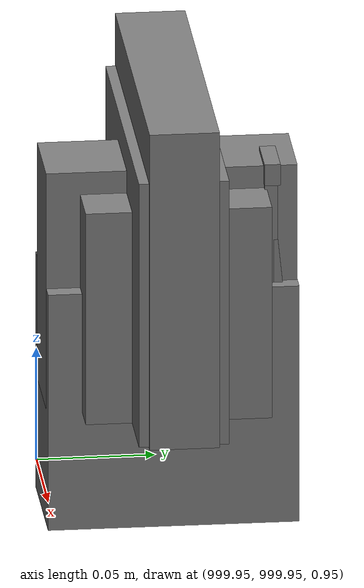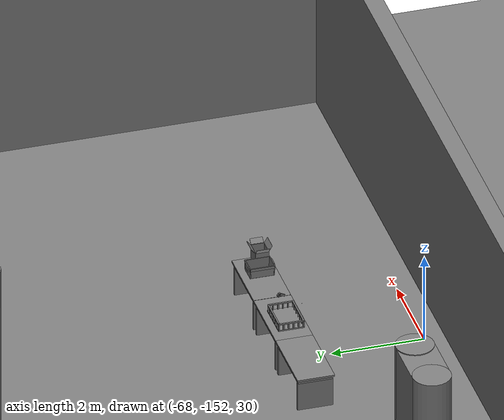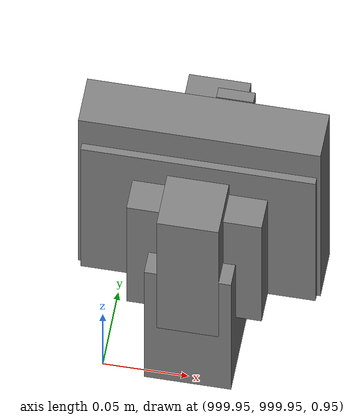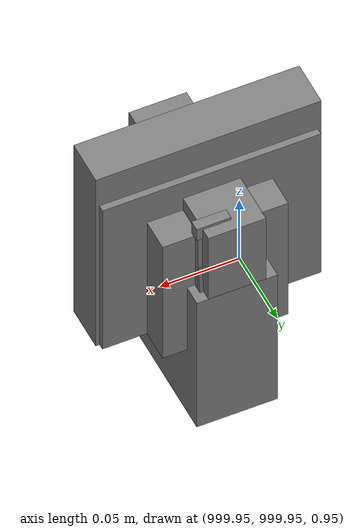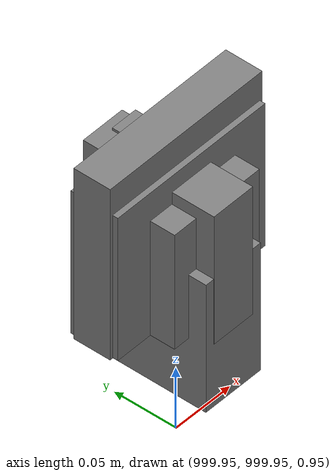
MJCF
<mujoco>
    <option gravity="0.000000000 0.000000000 -9.810000420" timestep="0.0049999999" integrator="implicitfast" density="1.225" viscosity="1.8000001e-05" noslip_iterations="10" iterations="100" sdf_iterations="50">
        <flag multiccd="disable"/>
    </option>
    <size memory="1000M"/>
    <compiler coordinate="local"/>
    <worldbody>
        <light cutoff="30" pos="0 1 1" dir="0 -1 -2"/>
        <light cutoff="30" pos="0 -1 1" dir="0 1 -2"/>
        <body pos="-64.866622925 -149.383972168 30.183746338" euler="89.999984741 89.999946594 0.000000000" name="openloong_gripper_2f85_fix_base_usda_bluebox_01">
            <geom contype="1" conaffinity="1" density="1000" type="box" material="" rgba="0.500000000 0.500000000 0.500000000 1.000000000" solimp="0.899999976 0.949999988 0.001000000" friction="1.000000000 0.005000000 0.000100000" solref="0.020000000 1.000000000" margin="0" condim="3" group="0" pos="0.276580811 0.187225342 0.000068665" quat="0.707106948 0.000077471 0.707106352 0.000077486" size="0.100000001 0.057999998 0.010000000" name="openloong_gripper_2f85_fix_base_usda_geom_FFDF66A3_E739_4380_BC8B_2EB8A87AB1B8"/>
            <geom contype="1" conaffinity="1" density="1000" type="box" material="" rgba="0.500000000 0.500000000 0.500000000 1.000000000" solimp="0.899999976 0.949999988 0.001000000" friction="1.000000000 0.005000000 0.000100000" solref="0.020000000 1.000000000" margin="0" condim="3" group="0" pos="0.000000000 0.002883911 0.000000000" quat="0.999999881 0.000000000 0.000000000 0.000000000" size="0.254000008 0.003000000 0.172000006" name="openloong_gripper_2f85_fix_base_usda_geom_C6C7D703_C178_4054_914C_96C053ED8FDF"/>
            <geom contype="1" conaffinity="1" density="1000" type="box" material="" rgba="0.500000000 0.500000000 0.500000000 1.000000000" solimp="0.899999976 0.949999988 0.001000000" friction="1.000000000 0.005000000 0.000100000" solref="0.020000000 1.000000000" margin="0" condim="3" group="0" pos="0.000000000 0.124874115 0.173484802" quat="0.999796331 0.020176515 -0.000000015 0.000000030" size="0.259999990 0.119999997 0.007000000" name="openloong_gripper_2f85_fix_base_usda_geom_F3581C15_9F93_4519_85AE_F086088005BB"/>
            <geom contype="1" conaffinity="1" density="1000" type="box" material="" rgba="0.500000000 0.500000000 0.500000000 1.000000000" solimp="0.899999976 0.949999988 0.001000000" friction="1.000000000 0.005000000 0.000100000" solref="0.020000000 1.000000000" margin="0" condim="3" group="0" pos="0.000000000 0.124874115 -0.173469543" quat="0.999796331 -0.020176545 -0.000000015 0.000000000" size="0.259999990 0.119999997 0.007000000" name="openloong_gripper_2f85_fix_base_usda_geom_A3A17AC7_0AA0_4211_8D90_1338C09CC276"/>
            <geom contype="1" conaffinity="1" density="1000" type="box" material="" rgba="0.500000000 0.500000000 0.500000000 1.000000000" solimp="0.899999976 0.949999988 0.001000000" friction="1.000000000 0.005000000 0.000100000" solref="0.020000000 1.000000000" margin="0" condim="3" group="0" pos="0.000000000 0.214008331 0.188980103" quat="0.999912977 0.013176724 0.000000015 0.000000000" size="0.259999990 0.029999999 0.012500000" name="openloong_gripper_2f85_fix_base_usda_geom_D8A800EA_02C9_45AF_8F92_AE30493798E4"/>
            <geom contype="1" conaffinity="1" density="1000" type="box" material="" rgba="0.500000000 0.500000000 0.500000000 1.000000000" solimp="0.899999976 0.949999988 0.001000000" friction="1.000000000 0.005000000 0.000100000" solref="0.020000000 1.000000000" margin="0" condim="3" group="0" pos="-0.258361816 0.125289917 0.001876831" quat="0.702796936 -0.020792112 0.710783124 0.020769298" size="0.189999998 0.119999997 0.009000000" name="openloong_gripper_2f85_fix_base_usda_geom_CAB51EAB_10FA_445D_8A9E_38F16CF8F3E9"/>
            <geom contype="1" conaffinity="1" density="1000" type="box" material="" rgba="0.500000000 0.500000000 0.500000000 1.000000000" solimp="0.899999976 0.949999988 0.001000000" friction="1.000000000 0.005000000 0.000100000" solref="0.020000000 1.000000000" margin="0" condim="3" group="0" pos="0.000000000 0.214008331 -0.188980103" quat="0.999912977 -0.013176769 0.000000030 0.000000015" size="0.259999990 0.029999999 0.012500000" name="openloong_gripper_2f85_fix_base_usda_geom_46011A0A_AAA1_4713_9E8D_1E12ED240DD9"/>
            <geom contype="1" conaffinity="1" density="1000" type="box" material="" rgba="0.500000000 0.500000000 0.500000000 1.000000000" solimp="0.899999976 0.949999988 0.001000000" friction="1.000000000 0.005000000 0.000100000" solref="0.020000000 1.000000000" margin="0" condim="3" group="0" pos="-0.276611328 0.187225342 0.000068665" quat="0.707106650 0.000077441 0.707106709 0.000077456" size="0.100000001 0.057999998 0.010000000" name="openloong_gripper_2f85_fix_base_usda_geom_530CC8E0_60A5_4E1C_A665_FAD37C17DA81"/>
            <geom contype="1" conaffinity="1" density="1000" type="box" material="" rgba="0.500000000 0.500000000 0.500000000 1.000000000" solimp="0.899999976 0.949999988 0.001000000" friction="1.000000000 0.005000000 0.000100000" solref="0.020000000 1.000000000" margin="0" condim="3" group="0" pos="0.258331299 0.125289917 0.001876831" quat="0.702851415 0.018856421 0.710823774 -0.019329369" size="0.189999998 0.119999997 0.009000000" name="openloong_gripper_2f85_fix_base_usda_geom_D7BFF1C6_19F2_4044_967B_BE1CD8FC09E2"/>
            <freejoint name="openloong_gripper_2f85_fix_base_usda_bluebox_01_joint"/>
            <site size="0.005000000 0.005000000 0.005000000" rgba="0.500000000 0.500000000 0.500000000 1.000000000" pos="0.000000000 0.000000000 0.000000000" quat="0.999961913 0.008726534 0.000000000 0.000000000" group="0" type="sphere" name="openloong_gripper_2f85_fix_base_usda_bluebox_01site"/>
        </body>
        <body pos="-64.496299744 -149.491867065 30.235729218" euler="0.000000000 0.000000000 89.999946594" name="openloong_gripper_2f85_fix_base_usda_cardboardbox_01">
            <geom contype="1" conaffinity="1" density="1000" type="box" material="" rgba="0.500000000 0.500000000 0.500000000 1.000000000" solimp="0.899999976 0.949999988 0.001000000" friction="1.000000000 0.005000000 0.000100000" solref="0.020000000 1.000000000" margin="0" condim="3" group="0" pos="-0.003166199 -0.004086494 0.005052090" quat="1.000000000 0.000000000 0.000000000 0.000000000" size="0.142499998 0.177500010 0.005000000" name="openloong_gripper_2f85_fix_base_usda_geom_D66D1256_0211_4E02_A983_B57B16689E50"/>
            <geom contype="1" conaffinity="1" density="1000" type="box" material="" rgba="0.500000000 0.500000000 0.500000000 1.000000000" solimp="0.899999976 0.949999988 0.001000000" friction="1.000000000 0.005000000 0.000100000" solref="0.020000000 1.000000000" margin="0" condim="3" group="0" pos="-0.003166199 0.170316696 0.150570869" quat="1.000000000 0.000000000 0.000000000 0.000000000" size="0.142499998 0.005000000 0.149999991" name="openloong_gripper_2f85_fix_base_usda_geom_87C43378_0B17_4F79_9A33_6F606778388D"/>
            <geom contype="1" conaffinity="1" density="1000" type="box" material="" rgba="0.500000000 0.500000000 0.500000000 1.000000000" solimp="0.899999976 0.949999988 0.001000000" friction="1.000000000 0.005000000 0.000100000" solref="0.020000000 1.000000000" margin="0" condim="3" group="0" pos="-0.147399902 -0.005307198 0.150570869" quat="1.000000000 0.000000000 0.000000000 0.000000000" size="0.005000000 0.177500010 0.149999991" name="openloong_gripper_2f85_fix_base_usda_geom_77444D83_C4EA_492C_BDC7_5DB35AC43F44"/>
            <geom contype="1" conaffinity="1" density="1000" type="box" material="" rgba="0.500000000 0.500000000 0.500000000 1.000000000" solimp="0.899999976 0.949999988 0.001000000" friction="1.000000000 0.005000000 0.000100000" solref="0.020000000 1.000000000" margin="0" condim="3" group="0" pos="0.140275955 -0.005307198 0.150570869" quat="1.000000000 0.000000000 0.000000000 0.000000000" size="0.005000000 0.177500010 0.149999991" name="openloong_gripper_2f85_fix_base_usda_geom_1233301B_D47D_40C2_B3B2_F268D8C992BE"/>
            <geom contype="1" conaffinity="1" density="1000" type="box" material="" rgba="0.500000000 0.500000000 0.500000000 1.000000000" solimp="0.899999976 0.949999988 0.001000000" friction="1.000000000 0.005000000 0.000100000" solref="0.020000000 1.000000000" margin="0" condim="3" group="0" pos="-0.003166199 -0.181550980 0.150570869" quat="1.000000000 0.000000000 0.000000000 0.000000000" size="0.142499998 0.005000000 0.149999991" name="openloong_gripper_2f85_fix_base_usda_geom_430304CC_D527_4444_BB1F_A64ACDA0B6F3"/>
            <freejoint name="openloong_gripper_2f85_fix_base_usda_cardboardbox_01_joint"/>
            <site size="0.005000000 0.005000000 0.005000000" rgba="0.500000000 0.500000000 0.500000000 1.000000000" pos="0.000000000 0.000000000 0.000000000" quat="0.999961913 0.008726535 0.000000000 0.000000000" group="0" type="sphere" name="openloong_gripper_2f85_fix_base_usda_site_5CCA7745_8940_492E_B187_E89A9AA84556"/>
            <body pos="0.139160156 -0.004048347 0.301930904" euler="-179.999954224 49.383502960 179.999954224" name="openloong_gripper_2f85_fix_base_usda_A1_006">
                <geom contype="1" conaffinity="1" density="1000" type="box" material="" rgba="0.500000000 0.500000000 0.500000000 1.000000000" solimp="0.899999976 0.949999988 0.001000000" friction="1.000000000 0.005000000 0.000100000" solref="0.020000000 1.000000000" margin="0" condim="3" group="0" pos="-0.071587563 0.000009537 0.001745224" quat="0.999999881 0.000000000 0.000000000 0.000000000" size="0.071249999 0.179999992 0.002500000" name="openloong_gripper_2f85_fix_base_usda_geom_FFB34B9A_D38F_4B78_BBCF_1059DA4CBFF8"/>
                <joint armature="0" stiffness="0.07" damping="0.0099999998" axis="0.000000 1.000000 0.000000" type="hinge" name="openloong_gripper_2f85_fix_base_usda_A1_006"/>
            </body>
            <body pos="-0.145902634 -0.004086494 0.301938057" euler="-180.000000000 -60.000011444 -180.000000000" name="openloong_gripper_2f85_fix_base_usda_A2_006">
                <geom contype="1" conaffinity="1" density="1000" type="box" material="" rgba="0.500000000 0.500000000 0.500000000 1.000000000" solimp="0.899999976 0.949999988 0.001000000" friction="1.000000000 0.005000000 0.000100000" solref="0.020000000 1.000000000" margin="0" condim="3" group="0" pos="0.071268082 0.000009537 0.002717972" quat="0.000002921 0.000000000 -0.000000030 0.999999881" size="0.071249999 0.179999992 0.002500000" name="openloong_gripper_2f85_fix_base_usda_geom_A97CD274_8273_4A1F_815B_B88468702FC9"/>
                <joint armature="0" stiffness="0.07" damping="0.0099999998" axis="0.000000 1.000000 0.000000" type="hinge" name="openloong_gripper_2f85_fix_base_usda_A2_006"/>
            </body>
            <body pos="-0.003385544 0.175991058 0.301930904" euler="-125.858116150 -0.000004561 0.000002331" name="openloong_gripper_2f85_fix_base_usda_B2_006">
                <geom contype="1" conaffinity="1" density="1000" type="box" material="" rgba="0.500000000 0.500000000 0.500000000 1.000000000" solimp="0.899999976 0.949999988 0.001000000" friction="1.000000000 0.005000000 0.000100000" solref="0.020000000 1.000000000" margin="0" condim="3" group="0" pos="0.000009537 -0.070939064 -0.002470016" quat="0.999614120 0.027776197 -0.000000015 0.000000030" size="0.137500003 0.064999998 0.005000000" name="openloong_gripper_2f85_fix_base_usda_geom_08C2B4C3_2A04_4C88_8FC6_EAD1FB877D7D"/>
                <joint armature="0" stiffness="0.07" damping="0.0099999998" axis="1.000000 0.000000 0.000000" type="hinge" name="openloong_gripper_2f85_fix_base_usda_B2_006"/>
            </body>
            <body pos="-0.003385544 -0.184140205 0.301938057" euler="147.805557251 0.000000000 0.000000000" name="openloong_gripper_2f85_fix_base_usda_B1_006">
                <geom contype="1" conaffinity="1" density="1000" type="box" material="" rgba="0.500000000 0.500000000 0.500000000 1.000000000" solimp="0.899999976 0.949999988 0.001000000" friction="1.000000000 0.005000000 0.000100000" solref="0.020000000 1.000000000" margin="0" condim="3" group="0" pos="-0.000028610 0.070202351 -0.002703667" quat="0.999614179 -0.027776167 0.000000000 0.000000000" size="0.137500003 0.064999998 0.005000000" name="openloong_gripper_2f85_fix_base_usda_geom_545AB4CB_54F8_49B0_822D_51336A371524"/>
                <joint armature="0" stiffness="0.07" damping="0.0099999998" axis="1.000000 0.000000 0.000000" type="hinge" name="openloong_gripper_2f85_fix_base_usda_B1_006"/>
            </body>
        </body>
        <body pos="-65.882858276 -149.481979370 30.229999542" euler="-64.487716675 0.000000000 0.000000000" name="openloong_gripper_2f85_fix_base_usda_Barcode">
            <geom contype="1" conaffinity="1" density="1000" type="box" material="" rgba="0.500000000 0.500000000 0.500000000 1.000000000" solimp="0.899999976 0.949999988 0.001000000" friction="1.000000000 0.005000000 0.000100000" solref="0.020000000 1.000000000" margin="0" condim="3" group="0" pos="0.000000000 0.013038635 0.001419067" quat="0.000000000 0.000000000 0.000000000 1.000000119" size="0.034000002 0.010000000 0.017999999" name="openloong_gripper_2f85_fix_base_usda_geom_306962E7_B259_44D5_9B0C_7D77C6F1D34E"/>
            <geom contype="1" conaffinity="1" density="1000" type="box" material="" rgba="0.500000000 0.500000000 0.500000000 1.000000000" solimp="0.899999976 0.949999988 0.001000000" friction="1.000000000 0.005000000 0.000100000" solref="0.020000000 1.000000000" margin="0" condim="3" group="0" pos="0.000000000 -0.035301208 -0.007095337" quat="0.000000000 0.000000000 -0.043619365 0.999048233" size="0.028999999 0.010000000 0.020000000" name="openloong_gripper_2f85_fix_base_usda_geom_6BE8260B_1B86_44B7_BE88_8516E17318B3"/>
            <geom contype="1" conaffinity="1" density="1000" type="box" material="" rgba="0.500000000 0.500000000 0.500000000 1.000000000" solimp="0.899999976 0.949999988 0.001000000" friction="1.000000000 0.005000000 0.000100000" solref="0.020000000 1.000000000" margin="0" condim="3" group="0" pos="0.000000000 -0.043411255 -0.011749268" quat="0.922262907 0.386563420 0.000000000 0.000000000" size="0.026000001 0.010000000 0.020000000" name="openloong_gripper_2f85_fix_base_usda_geom_F155A162_B81E_4A58_AD83_3DA175BECD49"/>
            <geom contype="1" conaffinity="1" density="1000" type="box" material="" rgba="0.500000000 0.500000000 0.500000000 1.000000000" solimp="0.899999976 0.949999988 0.001000000" friction="1.000000000 0.005000000 0.000100000" solref="0.020000000 1.000000000" margin="0" condim="3" group="0" pos="0.000000000 -0.016967773 -0.031860352" quat="0.000000000 0.000000000 0.000000000 1.000000119" size="0.008000000 0.010000000 0.013000000" name="openloong_gripper_2f85_fix_base_usda_geom_205BFAA3_7897_4CC6_90D1_C181856B43E6"/>
            <geom contype="1" conaffinity="1" density="1000" type="box" material="" rgba="0.500000000 0.500000000 0.500000000 1.000000000" solimp="0.899999976 0.949999988 0.001000000" friction="1.000000000 0.005000000 0.000100000" solref="0.020000000 1.000000000" margin="0" condim="3" group="0" pos="0.000000000 -0.001869202 0.000312805" quat="0.953716993 0.300705761 0.000000000 0.000000000" size="0.032000002 0.010000000 0.018999999" name="openloong_gripper_2f85_fix_base_usda_geom_19EE6C1A_35C2_4752_AB77_2B969816DBF3"/>
            <geom contype="1" conaffinity="1" density="1000" type="box" material="" rgba="0.500000000 0.500000000 0.500000000 1.000000000" solimp="0.899999976 0.949999988 0.001000000" friction="1.000000000 0.005000000 0.000100000" solref="0.020000000 1.000000000" margin="0" condim="3" group="0" pos="0.000000000 -0.019531250 -0.003173828" quat="0.953716993 0.300705761 0.000000000 0.000000000" size="0.030999999 0.010000000 0.020000000" name="openloong_gripper_2f85_fix_base_usda_geom_1E190722_1F7A_4DE4_A4FD_F29AF466569F"/>
            <geom contype="1" conaffinity="1" density="1000" type="box" material="" rgba="0.500000000 0.500000000 0.500000000 1.000000000" solimp="0.899999976 0.949999988 0.001000000" friction="1.000000000 0.005000000 0.000100000" solref="0.020000000 1.000000000" margin="0" condim="3" group="0" pos="0.000000000 -0.035301208 -0.007095337" quat="0.953716993 0.300705761 0.000000000 0.000000000" size="0.028999999 0.010000000 0.020000000" name="openloong_gripper_2f85_fix_base_usda_geom_D04C998B_B658_4219_A4F7_AD3FE9A9EE31"/>
            <geom contype="1" conaffinity="1" density="1000" type="box" material="" rgba="0.500000000 0.500000000 0.500000000 1.000000000" solimp="0.899999976 0.949999988 0.001000000" friction="1.000000000 0.005000000 0.000100000" solref="0.020000000 1.000000000" margin="0" condim="3" group="0" pos="0.000000000 -0.042617798 -0.071121216" quat="0.000000000 0.000000000 0.000000000 1.000000119" size="0.013000000 0.021000000 0.059999999" name="openloong_gripper_2f85_fix_base_usda_geom_02298C40_0549_408C_A97B_CC113A3F1AD0"/>
            <freejoint name="openloong_gripper_2f85_fix_base_usda_Barcode_joint"/>
            <site size="0.005000000 0.005000000 0.005000000" rgba="0.500000000 0.500000000 0.500000000 1.000000000" pos="0.000000000 0.000000000 0.000000000" quat="1.000000000 0.000000000 0.000000000 0.000000000" group="0" type="sphere" name="openloong_gripper_2f85_fix_base_usda_Barcode_site"/>
        </body>
        <body pos="-66.745018005 -149.392349243 30.184000015" euler="0.000000000 0.000000000 89.999946594" name="[22330357268396]_Basket_01">
            <geom contype="1" conaffinity="1" density="1000" type="box" material="" rgba="0.500000000 0.500000000 0.500000000 1.000000000" solimp="0.899999976 0.949999988 0.001000000" friction="1.000000000 0.005000000 0.000100000" solref="0.020000000 1.000000000" margin="0" condim="3" group="0" pos="-0.052425385 0.389207840 0.089787483" quat="0.707107008 0.000000000 0.000000000 0.707106411" size="0.014249999 0.014249999 0.059999999" name="[22330357268396]_geom_19ECE6DD_D9C3_4193_A0C6_F335F3D74F8D"/>
            <geom contype="1" conaffinity="1" density="1000" type="box" material="" rgba="0.500000000 0.500000000 0.500000000 1.000000000" solimp="0.899999976 0.949999988 0.001000000" friction="1.000000000 0.005000000 0.000100000" solref="0.020000000 1.000000000" margin="0" condim="3" group="0" pos="0.264015198 -0.133043289 0.089787483" quat="0.707107008 0.000000000 0.000000000 0.707106411" size="0.014249999 0.014249999 0.059999999" name="[22330357268396]_geom_5E178056_E024_4419_851C_CDC69C9BA668"/>
            <geom contype="1" conaffinity="1" density="1000" type="box" material="" rgba="0.500000000 0.500000000 0.500000000 1.000000000" solimp="0.899999976 0.949999988 0.001000000" friction="1.000000000 0.005000000 0.000100000" solref="0.020000000 1.000000000" margin="0" condim="3" group="0" pos="-0.264015198 -0.265548706 0.089793205" quat="0.707107008 0.000000000 0.000000000 0.707106411" size="0.014249999 0.014249999 0.059999999" name="[22330357268396]_geom_0F012557_778F_4102_B9B5_BF3D666944D4"/>
            <geom contype="1" conaffinity="1" density="1000" type="box" material="" rgba="0.500000000 0.500000000 0.500000000 1.000000000" solimp="0.899999976 0.949999988 0.001000000" friction="1.000000000 0.005000000 0.000100000" solref="0.020000000 1.000000000" margin="0" condim="3" group="0" pos="-0.160263062 -0.389322281 0.089793205" quat="0.707107008 0.000000000 0.000000000 0.707106411" size="0.014249999 0.014249999 0.059999999" name="[22330357268396]_geom_AA55F30E_9DE5_4001_B0E3_02E4C1DFDAC0"/>
            <geom contype="1" conaffinity="1" density="1000" type="box" material="" rgba="0.500000000 0.500000000 0.500000000 1.000000000" solimp="0.899999976 0.949999988 0.001000000" friction="1.000000000 0.005000000 0.000100000" solref="0.020000000 1.000000000" margin="0" condim="3" group="0" pos="0.162265778 -0.389322281 0.089787483" quat="0.707107008 0.000000000 0.000000000 0.707106411" size="0.014249999 0.014249999 0.059999999" name="[22330357268396]_geom_2C96106C_F183_4C76_83D3_A1F87BE9B3A8"/>
            <geom contype="1" conaffinity="1" density="1000" type="box" material="" rgba="0.500000000 0.500000000 0.500000000 1.000000000" solimp="0.899999976 0.949999988 0.001000000" friction="1.000000000 0.005000000 0.000100000" solref="0.020000000 1.000000000" margin="0" condim="3" group="0" pos="0.264015198 0.389207840 0.089787483" quat="0.707107008 0.000000000 0.000000000 0.707106411" size="0.014249999 0.014249999 0.059999999" name="[22330357268396]_geom_7BB8806C_2E4F_4B8F_88FA_F8E8889C8357"/>
            <geom contype="1" conaffinity="1" density="1000" type="box" material="" rgba="0.500000000 0.500000000 0.500000000 1.000000000" solimp="0.899999976 0.949999988 0.001000000" friction="1.000000000 0.005000000 0.000100000" solref="0.020000000 1.000000000" margin="0" condim="3" group="0" pos="-0.264015198 -0.133043289 0.089793205" quat="0.707107008 0.000000000 0.000000000 0.707106411" size="0.014249999 0.014249999 0.059999999" name="[22330357268396]_geom_C1F7447A_8EAD_47CD_81DD_A34DD95C89C3"/>
            <geom contype="1" conaffinity="1" density="1000" type="box" material="" rgba="0.500000000 0.500000000 0.500000000 1.000000000" solimp="0.899999976 0.949999988 0.001000000" friction="1.000000000 0.005000000 0.000100000" solref="0.020000000 1.000000000" margin="0" condim="3" group="0" pos="-0.264026642 0.269256592 0.089793205" quat="0.707107008 0.000000000 0.000000000 0.707106411" size="0.014249999 0.014249999 0.059999999" name="[22330357268396]_geom_58951D12_4632_4318_A1EC_BAF1D9B43C17"/>
            <geom contype="1" conaffinity="1" density="1000" type="box" material="" rgba="0.500000000 0.500000000 0.500000000 1.000000000" solimp="0.899999976 0.949999988 0.001000000" friction="1.000000000 0.005000000 0.000100000" solref="0.020000000 1.000000000" margin="0" condim="3" group="0" pos="0.054462433 0.389207840 0.089787483" quat="0.707107008 0.000000000 0.000000000 0.707106411" size="0.014249999 0.014249999 0.059999999" name="[22330357268396]_geom_2CC4AA5E_5686_4DCE_B3B3_5D0FD0E57416"/>
            <geom contype="1" conaffinity="1" density="1000" type="box" material="" rgba="0.500000000 0.500000000 0.500000000 1.000000000" solimp="0.899999976 0.949999988 0.001000000" friction="1.000000000 0.005000000 0.000100000" solref="0.020000000 1.000000000" margin="0" condim="3" group="0" pos="0.054462433 -0.389322281 0.089787483" quat="0.707107008 0.000000000 0.000000000 0.707106411" size="0.014249999 0.014249999 0.059999999" name="[22330357268396]_geom_64A29937_EBB3_4BDB_B2C3_3E24D26B2F24"/>
            <geom contype="1" conaffinity="1" density="1000" type="box" material="" rgba="0.500000000 0.500000000 0.500000000 1.000000000" solimp="0.899999976 0.949999988 0.001000000" friction="1.000000000 0.005000000 0.000100000" solref="0.020000000 1.000000000" margin="0" condim="3" group="0" pos="0.264015198 0.269256592 0.089793205" quat="0.707107008 0.000000000 0.000000000 0.707106411" size="0.014249999 0.014249999 0.059999999" name="[22330357268396]_geom_FBB9F7D5_2262_417A_A917_89941B55DB0C"/>
            <geom contype="1" conaffinity="1" density="1000" type="box" material="" rgba="0.500000000 0.500000000 0.500000000 1.000000000" solimp="0.899999976 0.949999988 0.001000000" friction="1.000000000 0.005000000 0.000100000" solref="0.020000000 1.000000000" margin="0" condim="3" group="0" pos="0.264015198 -0.389322281 0.089787483" quat="0.707107008 0.000000000 0.000000000 0.707106411" size="0.014249999 0.014249999 0.059999999" name="[22330357268396]_geom_A1E2F477_5C7D_468A_9F7F_7D226957F97A"/>
            <geom contype="1" conaffinity="1" density="1000" type="box" material="" rgba="0.500000000 0.500000000 0.500000000 1.000000000" solimp="0.899999976 0.949999988 0.001000000" friction="1.000000000 0.005000000 0.000100000" solref="0.020000000 1.000000000" margin="0" condim="3" group="0" pos="0.000000000 0.000000000 0.015998840" quat="0.707107008 0.000000000 0.000000000 0.707106411" size="0.403499991 0.279000014 0.015750000" name="[22330357268396]_geom_278BFF53_DD37_453A_A48A_1165FAEBD0B0"/>
            <geom contype="1" conaffinity="1" density="1000" type="box" material="" rgba="0.500000000 0.500000000 0.500000000 1.000000000" solimp="0.899999976 0.949999988 0.001000000" friction="1.000000000 0.005000000 0.000100000" solref="0.020000000 1.000000000" margin="0" condim="3" group="0" pos="0.000000000 -0.389476776 0.163619041" quat="0.707107008 0.000000000 0.000000000 0.707106411" size="0.015000000 0.277500004 0.015750000" name="[22330357268396]_geom_28C1E9B4_FB95_49E9_B981_A2357E13833B"/>
            <geom contype="1" conaffinity="1" density="1000" type="box" material="" rgba="0.500000000 0.500000000 0.500000000 1.000000000" solimp="0.899999976 0.949999988 0.001000000" friction="1.000000000 0.005000000 0.000100000" solref="0.020000000 1.000000000" margin="0" condim="3" group="0" pos="0.162265778 0.389207840 0.089787483" quat="0.707107008 0.000000000 0.000000000 0.707106411" size="0.014249999 0.014249999 0.059999999" name="[22330357268396]_geom_F15B12E8_AE21_4C18_918E_FA84E35D27EF"/>
            <geom contype="1" conaffinity="1" density="1000" type="box" material="" rgba="0.500000000 0.500000000 0.500000000 1.000000000" solimp="0.899999976 0.949999988 0.001000000" friction="1.000000000 0.005000000 0.000100000" solref="0.020000000 1.000000000" margin="0" condim="3" group="0" pos="0.000000000 0.389471054 0.163619041" quat="0.707107008 0.000000000 0.000000000 0.707106411" size="0.015000000 0.277500004 0.015750000" name="[22330357268396]_geom_8B07AD63_52F6_4412_B44F_F7D2407BD41A"/>
            <geom contype="1" conaffinity="1" density="1000" type="box" material="" rgba="0.500000000 0.500000000 0.500000000 1.000000000" solimp="0.899999976 0.949999988 0.001000000" friction="1.000000000 0.005000000 0.000100000" solref="0.020000000 1.000000000" margin="0" condim="3" group="0" pos="-0.263511658 0.000000000 0.163619041" quat="0.707107008 0.000000000 0.000000000 0.707106411" size="0.403499991 0.015000000 0.015750000" name="[22330357268396]_geom_BF28F8C8_8A83_4C85_87B9_8C80C91A061F"/>
            <geom contype="1" conaffinity="1" density="1000" type="box" material="" rgba="0.500000000 0.500000000 0.500000000 1.000000000" solimp="0.899999976 0.949999988 0.001000000" friction="1.000000000 0.005000000 0.000100000" solref="0.020000000 1.000000000" margin="0" condim="3" group="0" pos="-0.264015198 0.141334534 0.089793205" quat="0.707107008 0.000000000 0.000000000 0.707106411" size="0.014249999 0.014249999 0.059999999" name="[22330357268396]_geom_8D552A33_EEE0_4AD4_9082_1C915B8DB5D7"/>
            <geom contype="1" conaffinity="1" density="1000" type="box" material="" rgba="0.500000000 0.500000000 0.500000000 1.000000000" solimp="0.899999976 0.949999988 0.001000000" friction="1.000000000 0.005000000 0.000100000" solref="0.020000000 1.000000000" margin="0" condim="3" group="0" pos="0.264015198 -0.265548706 0.089787483" quat="0.707107008 0.000000000 0.000000000 0.707106411" size="0.014249999 0.014249999 0.059999999" name="[22330357268396]_geom_291DB1F3_188B_4872_B5AE_13EB12B67352"/>
            <geom contype="1" conaffinity="1" density="1000" type="box" material="" rgba="0.500000000 0.500000000 0.500000000 1.000000000" solimp="0.899999976 0.949999988 0.001000000" friction="1.000000000 0.005000000 0.000100000" solref="0.020000000 1.000000000" margin="0" condim="3" group="0" pos="-0.160263062 0.389207840 0.089787483" quat="0.707107008 0.000000000 0.000000000 0.707106411" size="0.014249999 0.014249999 0.059999999" name="[22330357268396]_geom_BBECC4B4_402A_41E4_B5ED_230D4D37C4F9"/>
            <geom contype="1" conaffinity="1" density="1000" type="box" material="" rgba="0.500000000 0.500000000 0.500000000 1.000000000" solimp="0.899999976 0.949999988 0.001000000" friction="1.000000000 0.005000000 0.000100000" solref="0.020000000 1.000000000" margin="0" condim="3" group="0" pos="-0.052425385 -0.389322281 0.089787483" quat="0.707107008 0.000000000 0.000000000 0.707106411" size="0.014249999 0.014249999 0.059999999" name="[22330357268396]_geom_D77C1799_0AB6_4DDA_BF2B_6F736F5C2255"/>
            <geom contype="1" conaffinity="1" density="1000" type="box" material="" rgba="0.500000000 0.500000000 0.500000000 1.000000000" solimp="0.899999976 0.949999988 0.001000000" friction="1.000000000 0.005000000 0.000100000" solref="0.020000000 1.000000000" margin="0" condim="3" group="0" pos="-0.264026642 -0.389322281 0.089793205" quat="0.707107008 0.000000000 0.000000000 0.707106411" size="0.014249999 0.014249999 0.059999999" name="[22330357268396]_geom_CADD8D7F_5015_428F_8570_88ADC38540DE"/>
            <geom contype="1" conaffinity="1" density="1000" type="box" material="" rgba="0.500000000 0.500000000 0.500000000 1.000000000" solimp="0.899999976 0.949999988 0.001000000" friction="1.000000000 0.005000000 0.000100000" solref="0.020000000 1.000000000" margin="0" condim="3" group="0" pos="0.264015198 0.141334534 0.089787483" quat="0.707107008 0.000000000 0.000000000 0.707106411" size="0.014249999 0.014249999 0.059999999" name="[22330357268396]_geom_740A5D76_0B23_4F91_84B2_237C846FEBD8"/>
            <geom contype="1" conaffinity="1" density="1000" type="box" material="" rgba="0.500000000 0.500000000 0.500000000 1.000000000" solimp="0.899999976 0.949999988 0.001000000" friction="1.000000000 0.005000000 0.000100000" solref="0.020000000 1.000000000" margin="0" condim="3" group="0" pos="-0.264015198 0.389207840 0.089793205" quat="0.707107008 0.000000000 0.000000000 0.707106411" size="0.014249999 0.014249999 0.059999999" name="[22330357268396]_geom_38A160C0_B349_4A89_A0E6_33B6297C8B53"/>
            <geom contype="1" conaffinity="1" density="1000" type="box" material="" rgba="0.500000000 0.500000000 0.500000000 1.000000000" solimp="0.899999976 0.949999988 0.001000000" friction="1.000000000 0.005000000 0.000100000" solref="0.020000000 1.000000000" margin="0" condim="3" group="0" pos="0.264015198 0.004480362 0.089787483" quat="0.707107008 0.000000000 0.000000000 0.707106411" size="0.014249999 0.014249999 0.059999999" name="[22330357268396]_geom_A57A2312_2841_47F0_9D9A_78181FEE13BF"/>
            <geom contype="1" conaffinity="1" density="1000" type="box" material="" rgba="0.500000000 0.500000000 0.500000000 1.000000000" solimp="0.899999976 0.949999988 0.001000000" friction="1.000000000 0.005000000 0.000100000" solref="0.020000000 1.000000000" margin="0" condim="3" group="0" pos="0.263694763 -0.000011444 0.163619041" quat="0.707107008 0.000000000 0.000000000 0.707106411" size="0.403499991 0.015000000 0.015750000" name="[22330357268396]_geom_834FBE30_BA90_41EF_99DC_D4416EB9142E"/>
            <geom contype="1" conaffinity="1" density="1000" type="box" material="" rgba="0.500000000 0.500000000 0.500000000 1.000000000" solimp="0.899999976 0.949999988 0.001000000" friction="1.000000000 0.005000000 0.000100000" solref="0.020000000 1.000000000" margin="0" condim="3" group="0" pos="-0.264015198 0.004480362 0.089793205" quat="0.707107008 0.000000000 0.000000000 0.707106411" size="0.014249999 0.014249999 0.059999999" name="[22330357268396]_geom_3BF00BD2_6929_427C_9567_3A34112E34FC"/>
            <freejoint name="[22330357268396]_joint_6B42422A_BE3A_47A8_AD8A_1BC202FB63B0"/>
        </body>
        <body pos="0.000000000 0.000000000 0.000000000" euler="0.000000000 0.000000000 0.000000000" name="Static Objects_Static Objects">
            <geom contype="1" conaffinity="1" density="1000" type="box" material="" rgba="0.500000000 0.500000000 0.500000000 1.000000000" solimp="0.899999976 0.949999988 0.001000000" friction="1.000000000 0.005000000 0.000100000" solref="0.020000000 1.000000000" margin="0" condim="3" group="0" pos="-67.544113159 -149.365814209 29.727830887" quat="0.500000417 0.499999970 0.499999553 0.499999970" size="0.381000012 0.319999993 0.041000001" name="Static Objects_geom_55661DE8_DE8C_47A8_A93A_0E99340FDC89"/>
            <geom contype="1" conaffinity="1" density="1000" type="box" material="" rgba="0.500000000 0.500000000 0.500000000 1.000000000" solimp="0.899999976 0.949999988 0.001000000" friction="1.000000000 0.005000000 0.000100000" solref="0.020000000 1.000000000" margin="0" condim="3" group="0" pos="-68.239501953 -149.365814209 30.086868286" quat="0.500000417 0.499999970 0.499999553 0.499999970" size="0.370999992 0.039500002 0.745000005" name="Static Objects_geom_AA1C21C2_C48B_41A1_9F38_E3A0E9232A03"/>
            <geom contype="1" conaffinity="1" density="1000" type="box" material="" rgba="0.500000000 0.500000000 0.500000000 1.000000000" solimp="0.899999976 0.949999988 0.001000000" friction="1.000000000 0.005000000 0.000100000" solref="0.020000000 1.000000000" margin="0" condim="3" group="0" pos="-68.239501953 -149.365814209 30.147235870" quat="0.500000417 0.499999970 0.499999553 0.499999970" size="0.400000006 0.022000000 0.800000012" name="Static Objects_geom_5F4B02E7_531B_4350_9142_AFBC9C8E3FE8"/>
            <geom contype="1" conaffinity="1" density="1000" type="box" material="" rgba="0.500000000 0.500000000 0.500000000 1.000000000" solimp="0.899999976 0.949999988 0.001000000" friction="1.000000000 0.005000000 0.000100000" solref="0.020000000 1.000000000" margin="0" condim="3" group="0" pos="-68.934890747 -149.365814209 29.727830887" quat="0.500000417 0.499999970 0.499999553 0.499999970" size="0.381000012 0.319999993 0.041000001" name="Static Objects_geom_B0932DEC_B36D_4569_BAB3_5B376C851745"/>
            <geom contype="1" conaffinity="1" density="1000" type="box" material="" rgba="0.500000000 0.500000000 0.500000000 1.000000000" solimp="0.899999976 0.949999988 0.001000000" friction="1.000000000 0.005000000 0.000100000" solref="0.020000000 1.000000000" margin="0" condim="3" group="0" pos="-68.239501953 -149.365814209 29.561563492" quat="0.500000417 0.499999970 0.499999553 0.499999970" size="0.020000000 0.022000000 0.660000026" name="Static Objects_geom_7E1E610E_3437_4624_9E4C_7656717CBB90"/>
            <geom contype="1" conaffinity="1" density="1000" type="box" material="" rgba="0.500000000 0.500000000 0.500000000 1.000000000" solimp="0.899999976 0.949999988 0.001000000" friction="1.000000000 0.005000000 0.000100000" solref="0.020000000 1.000000000" margin="0" condim="3" group="0" pos="-65.945671082 -149.365814209 29.727830887" quat="0.500000417 0.499999970 0.499999553 0.499999970" size="0.381000012 0.319999993 0.041000001" name="Static Objects_geom_D77AF441_CDA0_4A27_A71B_3C97C9712349"/>
            <geom contype="1" conaffinity="1" density="1000" type="box" material="" rgba="0.500000000 0.500000000 0.500000000 1.000000000" solimp="0.899999976 0.949999988 0.001000000" friction="1.000000000 0.005000000 0.000100000" solref="0.020000000 1.000000000" margin="0" condim="3" group="0" pos="-66.641059875 -149.365814209 30.086868286" quat="0.500000417 0.499999970 0.499999553 0.499999970" size="0.370999992 0.039500002 0.745000005" name="Static Objects_geom_3923159D_91EF_46E9_8573_816175C2E38E"/>
            <geom contype="1" conaffinity="1" density="1000" type="box" material="" rgba="0.500000000 0.500000000 0.500000000 1.000000000" solimp="0.899999976 0.949999988 0.001000000" friction="1.000000000 0.005000000 0.000100000" solref="0.020000000 1.000000000" margin="0" condim="3" group="0" pos="-66.641059875 -149.365814209 30.147235870" quat="0.500000417 0.499999970 0.499999553 0.499999970" size="0.400000006 0.022000000 0.800000012" name="Static Objects_geom_F4A306BF_FA5B_4A9A_A6C3_5FAE9E7AE92A"/>
            <geom contype="1" conaffinity="1" density="1000" type="box" material="" rgba="0.500000000 0.500000000 0.500000000 1.000000000" solimp="0.899999976 0.949999988 0.001000000" friction="1.000000000 0.005000000 0.000100000" solref="0.020000000 1.000000000" margin="0" condim="3" group="0" pos="-67.336448669 -149.365814209 29.727830887" quat="0.500000417 0.499999970 0.499999553 0.499999970" size="0.381000012 0.319999993 0.041000001" name="Static Objects_geom_1DB55E76_D867_4EC9_A542_609A3EDC93A3"/>
            <geom contype="1" conaffinity="1" density="1000" type="box" material="" rgba="0.500000000 0.500000000 0.500000000 1.000000000" solimp="0.899999976 0.949999988 0.001000000" friction="1.000000000 0.005000000 0.000100000" solref="0.020000000 1.000000000" margin="0" condim="3" group="0" pos="-66.641059875 -149.365814209 29.561563492" quat="0.500000417 0.499999970 0.499999553 0.499999970" size="0.020000000 0.022000000 0.660000026" name="Static Objects_geom_C4CC6E25_6830_4281_84FD_5E08AADEFB98"/>
            <geom contype="1" conaffinity="1" density="1000" type="box" material="" rgba="0.500000000 0.500000000 0.500000000 1.000000000" solimp="0.899999976 0.949999988 0.001000000" friction="1.000000000 0.005000000 0.000100000" solref="0.020000000 1.000000000" margin="0" condim="3" group="0" pos="-64.338577271 -149.365814209 29.727830887" quat="0.500000417 0.499999970 0.499999553 0.499999970" size="0.381000012 0.319999993 0.041000001" name="Static Objects_geom_A8794AFD_D36D_4AE6_8A28_D48C3C0818A0"/>
            <geom contype="1" conaffinity="1" density="1000" type="box" material="" rgba="0.500000000 0.500000000 0.500000000 1.000000000" solimp="0.899999976 0.949999988 0.001000000" friction="1.000000000 0.005000000 0.000100000" solref="0.020000000 1.000000000" margin="0" condim="3" group="0" pos="-65.033966064 -149.365814209 30.086868286" quat="0.500000417 0.499999970 0.499999553 0.499999970" size="0.370999992 0.039500002 0.745000005" name="Static Objects_geom_2598686C_1C69_4D51_81DD_FDAE24FE44FF"/>
            <geom contype="1" conaffinity="1" density="1000" type="box" material="" rgba="0.500000000 0.500000000 0.500000000 1.000000000" solimp="0.899999976 0.949999988 0.001000000" friction="1.000000000 0.005000000 0.000100000" solref="0.020000000 1.000000000" margin="0" condim="3" group="0" pos="-65.033966064 -149.365814209 30.147235870" quat="0.500000417 0.499999970 0.499999553 0.499999970" size="0.400000006 0.022000000 0.800000012" name="Static Objects_geom_AF7CD33F_A911_4C66_84EF_567278FF736D"/>
            <geom contype="1" conaffinity="1" density="1000" type="box" material="" rgba="0.500000000 0.500000000 0.500000000 1.000000000" solimp="0.899999976 0.949999988 0.001000000" friction="1.000000000 0.005000000 0.000100000" solref="0.020000000 1.000000000" margin="0" condim="3" group="0" pos="-65.729354858 -149.365814209 29.727830887" quat="0.500000417 0.499999970 0.499999553 0.499999970" size="0.381000012 0.319999993 0.041000001" name="Static Objects_geom_BE238FD2_88CF_407A_B5C2_203726A0850B"/>
            <geom contype="1" conaffinity="1" density="1000" type="box" material="" rgba="0.500000000 0.500000000 0.500000000 1.000000000" solimp="0.899999976 0.949999988 0.001000000" friction="1.000000000 0.005000000 0.000100000" solref="0.020000000 1.000000000" margin="0" condim="3" group="0" pos="-65.033966064 -149.365814209 29.561563492" quat="0.500000417 0.499999970 0.499999553 0.499999970" size="0.020000000 0.022000000 0.660000026" name="Static Objects_geom_0EA345AB_B7BA_41B0_BEE1_0F12CD14B454"/>
            <geom contype="1" conaffinity="1" density="1000" type="box" material="" rgba="0.500000000 0.500000000 0.500000000 1.000000000" solimp="0.899999976 0.949999988 0.001000000" friction="1.000000000 0.005000000 0.000100000" solref="0.020000000 1.000000000" margin="0" condim="3" group="0" pos="-61.754566193 -137.853729248 33.906845093" quat="0.707107067 0.000000000 0.000000000 0.707106471" size="0.759999990 0.759999990 4.500000000" name="Static Objects_geom_AED84DB3_EA5F_4830_8162_D8655C801625"/>
            <geom contype="1" conaffinity="1" density="1000" type="box" material="" rgba="0.500000000 0.500000000 0.500000000 1.000000000" solimp="0.899999976 0.949999988 0.001000000" friction="1.000000000 0.005000000 0.000100000" solref="0.020000000 1.000000000" margin="0" condim="3" group="0" pos="-57.511135101 -144.927108765 31.707921982" quat="1.000000000 0.000000000 0.000000000 0.000000000" size="0.200000003 8.000000000 2.299999952" name="Static Objects_geom_A024ED97_2998_490E_A1CC_487BF8775954"/>
            <geom contype="1" conaffinity="1" density="1000" type="box" material="" rgba="0.500000000 0.500000000 0.500000000 1.000000000" solimp="0.899999976 0.949999988 0.001000000" friction="1.000000000 0.005000000 0.000100000" solref="0.020000000 1.000000000" margin="0" condim="3" group="0" pos="-80.517646790 -157.574050903 31.688196182" quat="0.707107067 0.000000000 0.000000000 0.707106471" size="0.600000024 0.600000024 2.299999952" name="Static Objects_geom_633E3830_8906_4101_8C4B_A6B141762C89"/>
            <geom contype="1" conaffinity="1" density="1000" type="box" material="" rgba="0.500000000 0.500000000 0.500000000 1.000000000" solimp="0.899999976 0.949999988 0.001000000" friction="1.000000000 0.005000000 0.000100000" solref="0.020000000 1.000000000" margin="0" condim="3" group="0" pos="-80.711044312 -147.414932251 31.666158676" quat="1.000000000 0.000000000 0.000000000 0.000000000" size="0.200000003 10.000000000 2.299999952" name="Static Objects_geom_6B7B53DE_E51A_4819_8045_BF1F9CF49A25"/>
            <geom contype="1" conaffinity="1" density="1000" type="box" material="" rgba="0.500000000 0.500000000 0.500000000 1.000000000" solimp="0.899999976 0.949999988 0.001000000" friction="1.000000000 0.005000000 0.000100000" solref="0.020000000 1.000000000" margin="0" condim="3" group="0" pos="-57.687217712 -137.434692383 31.688196182" quat="0.707107067 0.000000000 0.000000000 0.707106471" size="0.600000024 0.600000024 2.299999952" name="Static Objects_geom_B21040FF_CA2A_4AA5_A34F_421A5FB25639"/>
            <geom contype="1" conaffinity="1" density="1000" type="box" material="" rgba="0.500000000 0.500000000 0.500000000 1.000000000" solimp="0.899999976 0.949999988 0.001000000" friction="1.000000000 0.005000000 0.000100000" solref="0.020000000 1.000000000" margin="0" condim="3" group="0" pos="-69.537033081 -140.263229370 31.714921951" quat="0.707107067 0.000000000 0.000000000 0.707106471" size="0.759999990 4.500000000 2.299999952" name="Static Objects_geom_CC940CB7_E741_44A9_80EE_1438CA55E4BD"/>
            <geom contype="1" conaffinity="1" density="1000" type="box" material="" rgba="0.500000000 0.500000000 0.500000000 1.000000000" solimp="0.899999976 0.949999988 0.001000000" friction="1.000000000 0.005000000 0.000100000" solref="0.020000000 1.000000000" margin="0" condim="3" group="0" pos="-80.073638916 -137.853713989 33.906845093" quat="0.707107067 0.000000000 0.000000000 0.707106471" size="0.759999990 0.759999990 4.500000000" name="Static Objects_geom_079A4B60_B31D_434F_83E9_EF945C8F03A4"/>
            <geom contype="1" conaffinity="1" density="1000" type="box" material="" rgba="0.500000000 0.500000000 0.500000000 1.000000000" solimp="0.899999976 0.949999988 0.001000000" friction="1.000000000 0.005000000 0.000100000" solref="0.020000000 1.000000000" margin="0" condim="3" group="0" pos="-73.406707764 -155.734664917 31.707921982" quat="1.000000000 0.000000000 0.000000000 0.000000000" size="0.200000003 3.000000000 2.299999952" name="Static Objects_geom_D4FE3995_4FD3_44E3_9EE7_6BFF24974A41"/>
            <geom contype="1" conaffinity="1" density="1000" type="box" material="" rgba="0.500000000 0.500000000 0.500000000 1.000000000" solimp="0.899999976 0.949999988 0.001000000" friction="1.000000000 0.005000000 0.000100000" solref="0.020000000 1.000000000" margin="0" condim="3" group="0" pos="-68.497543335 -137.448257446 31.707921982" quat="0.707107067 0.000000000 0.000000000 0.707106471" size="0.200000003 14.000000000 2.299999952" name="Static Objects_geom_9F9A5D7C_8B7A_4A2D_A9C9_243B1E461B90"/>
            <geom contype="1" conaffinity="1" density="1000" type="cylinder" material="" rgba="0.500000000 0.500000000 0.500000000 1.000000000" solimp="0.899999976 0.949999988 0.001000000" friction="1.000000000 0.005000000 0.000100000" solref="0.020000000 1.000000000" margin="0" condim="3" group="0" pos="-68.868522644 -142.134506226 31.711090088" quat="0.707107067 0.000000000 0.000000000 0.707106471" size="0.509999990 2.299999952 1.000000000" name="Static Objects_geom_FD942DC4_6FED_4555_9A83_655AD0A10D2F"/>
            <geom contype="1" conaffinity="1" density="1000" type="plane" material="" rgba="0.500000000 0.500000000 0.500000000 1.000000000" solimp="0.899999976 0.949999988 0.001000000" friction="1.000000000 0.005000000 0.000100000" solref="0.020000000 1.000000000" margin="0" condim="3" group="0" pos="-72.873703003 -147.131927490 29.409669876" quat="1.000000000 0.000000000 0.000000000 0.000000000" size="18.000000000 14.000000000 1.000000000" name="Static Objects_geom_5997E8B0_0D1A_4E05_A0F7_BE37CCB6AF2B"/>
            <geom contype="1" conaffinity="1" density="1000" type="box" material="" rgba="0.500000000 0.500000000 0.500000000 1.000000000" solimp="0.899999976 0.949999988 0.001000000" friction="1.000000000 0.005000000 0.000100000" solref="0.020000000 1.000000000" margin="0" condim="3" group="0" pos="-79.943580627 -157.782272339 31.707921982" quat="0.707107067 0.000000000 0.000000000 0.707106471" size="0.200000003 7.000000000 2.299999952" name="Static Objects_geom_EA5DEFA2_5BDB_47A2_A49B_463FD1A6620D"/>
            <geom contype="1" conaffinity="1" density="1000" type="box" material="" rgba="0.500000000 0.500000000 0.500000000 1.000000000" solimp="0.899999976 0.949999988 0.001000000" friction="1.000000000 0.005000000 0.000100000" solref="0.020000000 1.000000000" margin="0" condim="3" group="0" pos="-65.421028137 -152.903442383 31.707921982" quat="0.707107067 0.000000000 0.000000000 0.707106471" size="0.200000003 7.800000191 2.299999952" name="Static Objects_geom_A0F51DD6_35F8_4D05_A18C_818654867600"/>
            <geom contype="1" conaffinity="1" density="1000" type="box" material="" rgba="0.500000000 0.500000000 0.500000000 1.000000000" solimp="0.899999976 0.949999988 0.001000000" friction="1.000000000 0.005000000 0.000100000" solref="0.020000000 1.000000000" margin="0" condim="3" group="0" pos="-74.776908875 -149.964416504 31.688196182" quat="1.000000000 0.000000000 0.000000000 0.000000000" size="0.600000024 0.409999996 2.299999952" name="Static Objects_geom_BB7D522E_9958_4007_8884_FFE45799BC10"/>
            <geom contype="1" conaffinity="1" density="1000" type="cylinder" material="" rgba="0.500000000 0.500000000 0.500000000 1.000000000" solimp="0.899999976 0.949999988 0.001000000" friction="1.000000000 0.005000000 0.000100000" solref="0.020000000 1.000000000" margin="0" condim="3" group="0" pos="-60.161884308 -142.134506226 31.711090088" quat="0.707107067 0.000000000 0.000000000 0.707106471" size="0.509999990 2.299999952 1.000000000" name="Static Objects_geom_28ACFF19_ABDA_4E7C_9C6C_F03EC3E28288"/>
            <geom contype="1" conaffinity="1" density="1000" type="cylinder" material="" rgba="0.500000000 0.500000000 0.500000000 1.000000000" solimp="0.899999976 0.949999988 0.001000000" friction="1.000000000 0.005000000 0.000100000" solref="0.020000000 1.000000000" margin="0" condim="3" group="0" pos="-75.382453918 -149.963455200 31.711090088" quat="0.707107067 0.000000000 0.000000000 0.707106471" size="0.409999996 2.299999952 1.000000000" name="Static Objects_geom_D7695631_011C_4D66_8B8D_CF752268DB96"/>
            <geom contype="1" conaffinity="1" density="1000" type="cylinder" material="" rgba="0.500000000 0.500000000 0.500000000 1.000000000" solimp="0.899999976 0.949999988 0.001000000" friction="1.000000000 0.005000000 0.000100000" solref="0.020000000 1.000000000" margin="0" condim="3" group="0" pos="-74.154960632 -149.963455200 31.711090088" quat="0.707107067 0.000000000 0.000000000 0.707106471" size="0.409999996 2.299999952 1.000000000" name="Static Objects_geom_22D6CFF5_D57E_40B1_9E99_76935E92A54D"/>
            <geom contype="1" conaffinity="1" density="1000" type="cylinder" material="" rgba="0.500000000 0.500000000 0.500000000 1.000000000" solimp="0.899999976 0.949999988 0.001000000" friction="1.000000000 0.005000000 0.000100000" solref="0.020000000 1.000000000" margin="0" condim="3" group="0" pos="-77.566612244 -142.134506226 31.711090088" quat="0.707107067 0.000000000 0.000000000 0.707106471" size="0.509999990 2.299999952 1.000000000" name="Static Objects_geom_C66AEF90_E944_43CB_8E59_1825554E7DE8"/>
        </body>
        <body pos="1000.000000000 1000.000000000 1.000000000" euler="0.000000000 0.000000000 180.000000000" name="openloong_gripper_2f85_fix_base_usda_cpu_fan">
            <geom contype="1" conaffinity="1" density="1000" type="box" material="" rgba="0.500000000 0.500000000 0.500000000 1.000000000" solimp="0.899999976 0.949999988 0.001000000" friction="1.000000000 0.005000000 0.000100000" solref="0.020000000 1.000000000" margin="0" condim="3" group="0" pos="0.000000000 0.000000000 0.070034981" quat="0.000000000 0.000000000 0.000000000 1.000000000" size="0.070700005 0.014699999 0.070700005" name="openloong_gripper_2f85_fix_base_usda_geom_792E3D1D_18F5_4B2B_9051_A8A7E9B2348B"/>
            <freejoint name="openloong_gripper_2f85_fix_base_usda_cpu_fan_joint"/>
            <site size="0.005000000 0.005000000 0.005000000" rgba="0.500000000 0.500000000 0.500000000 1.000000000" pos="0.000000000 0.000000000 0.000000000" quat="0.999961913 0.008726535 0.000000000 0.000000000" group="0" type="sphere" name="openloong_gripper_2f85_fix_base_usda_cpu_fancsite"/>
        </body>
        <body pos="-66.131919861 -149.416702271 31.171951294" euler="1.440059662 -77.504127502 -1.140394926" mocap="true" name="spotlight1_SpotLight"/>
        <body pos="-66.203834534 -149.461456299 31.163015366" euler="160.356079102 -38.301269531 -31.775871277" mocap="true" name="spotlight3_SpotLight"/>
        <body pos="1000.000000000 1000.000000000 1.000000000" euler="0.000000000 0.000000000 180.000000000" name="openloong_gripper_2f85_fix_base_usda_battery_01">
            <geom contype="1" conaffinity="1" density="1000" type="box" material="" rgba="0.500000000 0.500000000 0.500000000 1.000000000" solimp="0.899999976 0.949999988 0.001000000" friction="1.000000000 0.005000000 0.000100000" solref="0.020000000 1.000000000" margin="0" condim="3" group="0" pos="-0.011123657 -0.041940309 0.101691343" quat="1.000000000 0.000000000 0.000000000 0.000000000" size="0.010800000 0.003375000 0.004725000" name="openloong_gripper_2f85_fix_base_usda_geom_FAC50A81_44B8_4D40_950A_436896D560D5"/>
            <geom contype="1" conaffinity="1" density="1000" type="box" material="" rgba="0.500000000 0.500000000 0.500000000 1.000000000" solimp="0.899999976 0.949999988 0.001000000" friction="1.000000000 0.005000000 0.000100000" solref="0.020000000 1.000000000" margin="0" condim="3" group="0" pos="-0.010876465 -0.044247437 0.047066893" quat="0.998702705 -0.050920475 0.000000000 0.000000000" size="0.009450001 0.002700000 0.024975000" name="openloong_gripper_2f85_fix_base_usda_geom_C29AF2D5_BF78_4EAD_A7C6_7AD5E77E92B6"/>
            <geom contype="1" conaffinity="1" density="1000" type="box" material="" rgba="0.500000000 0.500000000 0.500000000 1.000000000" solimp="0.899999976 0.949999988 0.001000000" friction="1.000000000 0.005000000 0.000100000" solref="0.020000000 1.000000000" margin="0" condim="3" group="0" pos="-0.001235962 -0.000659180 0.047381196" quat="1.000000000 0.000000000 0.000000000 0.000000000" size="0.039420001 0.039150000 0.047250003" name="openloong_gripper_2f85_fix_base_usda_geom_B8B5EDDD_116A_49E4_BB61_E93102FE7C12"/>
            <geom contype="1" conaffinity="1" density="1000" type="box" material="" rgba="0.500000000 0.500000000 0.500000000 1.000000000" solimp="0.899999976 0.949999988 0.001000000" friction="1.000000000 0.005000000 0.000100000" solref="0.020000000 1.000000000" margin="0" condim="3" group="0" pos="-0.010876465 -0.039138794 0.009851727" quat="1.000000000 0.000000000 0.000000000 0.000000000" size="0.009450001 0.010800000 0.013500000" name="openloong_gripper_2f85_fix_base_usda_geom_7C11A798_8310_42ED_9880_DBC65F806939"/>
            <geom contype="1" conaffinity="1" density="1000" type="box" material="" rgba="0.500000000 0.500000000 0.500000000 1.000000000" solimp="0.899999976 0.949999988 0.001000000" friction="1.000000000 0.005000000 0.000100000" solref="0.020000000 1.000000000" margin="0" condim="3" group="0" pos="-0.010876465 -0.041528322 0.071508206" quat="1.000000000 0.000000000 0.000000000 0.000000000" size="0.009450001 0.002700000 0.027000001" name="openloong_gripper_2f85_fix_base_usda_geom_B26EEFC0_D06C_4360_90C8_839B4F082A42"/>
            <freejoint name="openloong_gripper_2f85_fix_base_usda_battery_01_joint"/>
            <site size="0.005000000 0.005000000 0.005000000" rgba="0.500000000 0.500000000 0.500000000 1.000000000" pos="0.000000000 0.000000000 0.000000000" quat="0.999961913 0.008726500 0.000000000 0.000000000" group="0" type="sphere" name="openloong_gripper_2f85_fix_base_usda_battery_01site"/>
        </body>
        <body pos="1000.000000000 1000.000000000 1.000000000" euler="0.000000000 0.000000000 180.000000000" name="openloong_gripper_2f85_fix_base_usda_wifi_box">
            <geom contype="1" conaffinity="1" density="1000" type="box" material="" rgba="0.500000000 0.500000000 0.500000000 1.000000000" solimp="0.899999976 0.949999988 0.001000000" friction="1.000000000 0.005000000 0.000100000" solref="0.020000000 1.000000000" margin="0" condim="3" group="0" pos="0.000000000 0.000000000 0.058978677" quat="0.000000000 0.000000047 0.000000000 1.000000000" size="0.068499997 0.018999999 0.059000000" name="openloong_gripper_2f85_fix_base_usda_geom_B4C6E51B_FE07_4D86_AB9E_A87FBFC17771"/>
            <freejoint name="openloong_gripper_2f85_fix_base_usda_wifi_box_joint"/>
            <site size="0.005000000 0.005000000 0.005000000" rgba="0.500000000 0.500000000 0.500000000 1.000000000" pos="0.000000000 0.000000000 0.000000000" quat="0.999961913 0.008726500 0.000000000 0.000000000" group="0" type="sphere" name="openloong_gripper_2f85_fix_base_usda_wifi_boxsite"/>
        </body>
        <body pos="1000.000000000 1000.000000000 1.000000000" euler="0.000011953 0.000005123 -179.999984741" name="openloong_gripper_2f85_fix_base_usda_intel_box">
            <geom contype="1" conaffinity="1" density="1000" type="box" material="" rgba="0.500000000 0.500000000 0.500000000 1.000000000" solimp="0.899999976 0.949999988 0.001000000" friction="1.000000000 0.005000000 0.000100000" solref="0.020000000 1.000000000" margin="0" condim="3" group="0" pos="0.000000000 -0.000067139 0.000082284" quat="0.707106709 0.000000225 0.000000253 0.707106650" size="0.052800003 0.025300000 0.052800003" name="openloong_gripper_2f85_fix_base_usda_geom_073E1473_55C4_494F_8D3C_811DDF6C684C"/>
            <freejoint name="openloong_gripper_2f85_fix_base_usda_intel_box_joint"/>
            <site size="0.005000000 0.005000000 0.005000000" rgba="0.500000000 0.500000000 0.500000000 1.000000000" pos="0.000000000 0.000000000 0.000000000" quat="0.999961913 0.008726500 0.000000000 0.000000000" group="0" type="sphere" name="openloong_gripper_2f85_fix_base_usda_intel_boxsite"/>
        </body>
        <body pos="1000.000000000 999.999938965 1.000000000" euler="0.000000000 0.000000000 180.000000000" name="openloong_gripper_2f85_fix_base_usda_intelcore_i5">
            <geom contype="1" conaffinity="1" density="1000" type="box" material="" rgba="0.500000000 0.500000000 0.500000000 1.000000000" solimp="0.899999976 0.949999988 0.001000000" friction="1.000000000 0.005000000 0.000100000" solref="0.020000000 1.000000000" margin="0" condim="3" group="0" pos="0.000000000 0.000000000 0.051722717" quat="0.707106709 0.000000000 0.000000000 -0.707106769" size="0.052800000 0.018080002 0.052800000" name="openloong_gripper_2f85_fix_base_usda_geom_E692B6D4_29AF_4D69_A1DA_27EF44E053E4"/>
            <freejoint name="openloong_gripper_2f85_fix_base_usda_intelcore_i5_joint"/>
            <site size="0.005000000 0.005000000 0.005000000" rgba="0.500000000 0.500000000 0.500000000 1.000000000" pos="0.000000000 0.000000000 0.000000000" quat="0.999961913 0.008726534 0.000000000 0.000000000" group="0" type="sphere" name="openloong_gripper_2f85_fix_base_usda_intelcore_i5site"/>
        </body>
        <body pos="-66.278839111 -149.686645508 31.167961121" euler="121.211029053 -66.720390320 -179.364089966" mocap="true" name="spotlight2_SpotLight"/>
        <body pos="-66.291030884 -149.869689941 29.018842697" euler="0.000000000 0.000000000 89.999946594" mocap="true" name="openloong_gripper_2f85_fix_base_usda_leftHandMocap"/>
        <body pos="-66.291030884 -149.869689941 29.018842697" euler="0.000000000 0.000000000 89.999946594" mocap="true" name="openloong_gripper_2f85_fix_base_usda_rightHandMocap"/>
        <body pos="-66.291030884 -149.869689941 30.218843460" euler="0.000000000 0.000000000 89.999946594" name="openloong_gripper_2f85_fix_base_usda_base_link">
            <geom contype="1" conaffinity="1" density="1000" type="mesh" material="" rgba="0.783999979 0.783999979 0.783999979 1.000000000" solimp="0.899999976 0.949999988 0.001000000" friction="1.000000000 0.005000000 0.000100000" solref="0.020000000 1.000000000" margin="0" condim="3" group="3" mesh="base_link" pos="0.000000000 0.000000000 0.000000000" quat="1.000000000 0.000000000 0.000000000 0.000000000" size="1.000000000 1.000000000 1.000000000" name="openloong_gripper_2f85_fix_base_usda__geom_7_D9828E2B_BC8B_426E_A66B_1880F9C3175F"/>
            <site size="0.005000000 0.005000000 0.005000000" rgba="0.500000000 0.500000000 0.500000000 1.000000000" pos="0.000000000 0.000000000 0.000000000" quat="1.000000000 0.000000000 0.000000000 0.000000000" group="0" type="sphere" name="openloong_gripper_2f85_fix_base_usda_imu"/>
            <inertial mass="22.447001" pos="-0.005664100 -0.001336700 0.238289997" diaginertia="0.374352545 0.277180195 0.220617250" quat="0.999247074 0.035235517 -0.015086859 0.006023135"/>
            <body pos="0.000000000 0.000000000 0.299997330" euler="0.000000000 0.000000000 0.000000000" name="openloong_gripper_2f85_fix_base_usda_dummy_body">
                <geom contype="1" conaffinity="1" density="1000" type="sphere" material="" rgba="0.783999979 0.783999979 0.783999979 1.000000000" solimp="0.899999976 0.949999988 0.001000000" friction="1.000000000 0.005000000 0.000100000" solref="0.020000000 1.000000000" margin="0" condim="3" group="3" pos="0.000000000 0.000000000 0.000000000" quat="1.000000000 0.000000000 0.000000000 0.000000000" size="0.010000000 0.000000000 0.000000000" name="openloong_gripper_2f85_fix_base_usda__geom_8_0CE66494_35F7_423D_870A_A3B570266151"/>
                <joint armature="0.0099999998" stiffness="0" damping="0.1" axis="0.000000 0.000000 1.000000" type="hinge" name="openloong_gripper_2f85_fix_base_usda_dummy_joint"/>
                <site size="0.010000000 0.005000000 0.005000000" rgba="0.500000000 0.500000000 0.500000000 1.000000000" pos="0.000000000 0.000000000 0.000000000" quat="1.000000000 0.000000000 0.000000000 0.000000000" group="3" type="sphere" name="openloong_gripper_2f85_fix_base_usda_dummy_site"/>
            </body>
            <body pos="0.009002686 0.000000000 0.406400681" euler="0.000000000 0.000000000 0.000000000" name="openloong_gripper_2f85_fix_base_usda_Link_head_yaw">
                <geom contype="1" conaffinity="1" density="1000" type="mesh" material="" rgba="0.783999979 0.783999979 0.783999979 1.000000000" solimp="0.899999976 0.949999988 0.001000000" friction="1.000000000 0.005000000 0.000100000" solref="0.020000000 1.000000000" margin="0" condim="3" group="3" mesh="Link_head_yaw" pos="0.000000000 0.000000000 0.000000000" quat="1.000000000 0.000000000 0.000000000 0.000000000" size="1.000000000 1.000000000 1.000000000" name="openloong_gripper_2f85_fix_base_usda__geom_10_5DF7FFCF_9445_4A0F_AB25_A9C1AC0BCACE"/>
                <inertial mass="0.84249002" pos="0.000000000 -0.002081400 0.044801001" diaginertia="0.000700588 0.000629000 0.000553812" quat="0.706933022 -0.015675601 0.015677100 0.706933022"/>
                <body pos="0.000000000 -0.034599304 0.048500061" euler="0.000000000 0.000000000 0.000000000" name="openloong_gripper_2f85_fix_base_usda_Link_head_pitch">
                    <geom contype="1" conaffinity="1" density="1000" type="mesh" material="" rgba="0.783999979 0.783999979 0.783999979 1.000000000" solimp="0.899999976 0.949999988 0.001000000" friction="1.000000000 0.005000000 0.000100000" solref="0.020000000 1.000000000" margin="0" condim="3" group="3" mesh="Link_head_pitch" pos="0.000000000 0.000000000 0.000000000" quat="1.000000000 0.000000000 0.000000000 0.000000000" size="1.000000000 1.000000000 1.000000000" name="openloong_gripper_2f85_fix_base_usda__geom_12_C6D8BAB1_0ADA_4139_B09A_6727A30BF209"/>
                    <inertial mass="1.3943" pos="0.020569000 0.033004001 0.125000000" diaginertia="0.006381400 0.006289940 0.004481460" quat="0.973390222 0.008406822 0.228157058 0.019624906"/>
                    <body pos="0.000000000 0.029998779 0.000000000" euler="0.000000000 0.000000000 0.000000000" name="openloong_gripper_2f85_fix_base_usda_neck_center_body">
                        <site size="0.010000000 0.005000000 0.005000000" rgba="0.500000000 0.500000000 0.500000000 1.000000000" pos="0.000000000 0.000000000 0.000000000" quat="1.000000000 0.000000000 0.000000000 0.000000000" group="3" type="sphere" name="openloong_gripper_2f85_fix_base_usda_neck_center_site"/>
                        <body pos="0.020004272 0.000000000 0.149999619" euler="-0.000002229 39.998176575 -90.000205994" name="openloong_gripper_2f85_fix_base_usda_camera_head">
                            <site size="0.010000000 0.005000000 0.005000000" rgba="0.500000000 0.500000000 0.500000000 1.000000000" pos="0.000000000 0.000000000 0.000000000" quat="1.000000000 0.000000000 0.000000000 0.000000000" group="3" type="sphere" name="openloong_gripper_2f85_fix_base_usda_camera_head_site"/>
                        </body>
                    </body>
                </body>
            </body>
            <body pos="0.003997803 -0.161598206 0.392200470" euler="0.000000000 0.000000000 0.000000000" name="openloong_gripper_2f85_fix_base_usda_Link_arm_r_01">
                <geom contype="1" conaffinity="1" density="1000" type="mesh" material="" rgba="0.783999979 0.783999979 0.783999979 1.000000000" solimp="0.899999976 0.949999988 0.001000000" friction="1.000000000 0.005000000 0.000100000" solref="0.020000000 1.000000000" margin="0" condim="3" group="3" mesh="Link_arm_r_01" pos="0.000000000 0.000000000 0.000000000" quat="1.000000000 0.000000000 0.000000000 0.000000000" size="1.000000000 1.000000000 1.000000000" name="openloong_gripper_2f85_fix_base_usda__geom_14_8574DAB1_338A_4E7A_A15E_A709599CBB70"/>
                <joint armature="0.0099999998" stiffness="0" damping="1" axis="0.000000 -1.000000 0.000000" limited="true" range="-170.000015259 170.000015259" type="hinge" name="openloong_gripper_2f85_fix_base_usda_J_arm_r_01"/>
                <inertial mass="0.75641" pos="0.004494600 -0.038293999 -0.000001874" diaginertia="0.000842990 0.000803050 0.000587120" quat="-0.000163502 0.707098067 0.000812463 0.707115054"/>
                <body pos="-0.041992188 -0.041000366 0.000000000" euler="0.000000000 0.000000000 0.000000000" name="openloong_gripper_2f85_fix_base_usda_Link_arm_r_02">
                    <geom contype="1" conaffinity="1" density="1000" type="mesh" material="" rgba="0.783999979 0.783999979 0.783999979 1.000000000" solimp="0.899999976 0.949999988 0.001000000" friction="1.000000000 0.005000000 0.000100000" solref="0.020000000 1.000000000" margin="0" condim="3" group="3" mesh="Link_arm_r_02" pos="0.000000000 0.000000000 0.000000000" quat="1.000000000 0.000000000 0.000000000 0.000000000" size="1.000000000 1.000000000 1.000000000" name="openloong_gripper_2f85_fix_base_usda__geom_16_C0CEF6A2_2940_40BC_A9E7_03E143C311AC"/>
                    <joint armature="0.0099999998" stiffness="0" damping="1" axis="-1.000000 0.000000 0.000000" limited="true" range="-105.000244141 105.000244141" type="hinge" name="openloong_gripper_2f85_fix_base_usda_J_arm_r_02"/>
                    <inertial mass="0.98500001" pos="0.041999999 -0.067430697 0.000000000" diaginertia="0.002262690 0.001730990 0.001154020" quat="0.500000000 0.500000000 -0.500000000 0.500000000"/>
                    <body pos="0.041992188 -0.122596741 0.000000000" euler="0.000000000 0.000000000 0.000000000" name="openloong_gripper_2f85_fix_base_usda_Link_arm_r_03">
                        <geom contype="1" conaffinity="1" density="1000" type="mesh" material="" rgba="0.783999979 0.783999979 0.783999979 1.000000000" solimp="0.899999976 0.949999988 0.001000000" friction="1.000000000 0.005000000 0.000100000" solref="0.020000000 1.000000000" margin="0" condim="3" group="3" mesh="Link_arm_r_03" pos="0.000000000 0.000000000 0.000000000" quat="1.000000000 0.000000000 0.000000000 0.000000000" size="1.000000000 1.000000000 1.000000000" name="openloong_gripper_2f85_fix_base_usda__geom_18_331D6D1F_BE94_4C2E_B777_31BF2CECBCE5"/>
                        <joint armature="0.0099999998" stiffness="0" damping="1" axis="0.000000 -1.000000 0.000000" limited="true" range="-170.000015259 170.000015259" type="hinge" name="openloong_gripper_2f85_fix_base_usda_J_arm_r_03"/>
                        <inertial mass="0.95899999" pos="-0.001413580 -0.164663002 0.020757901" diaginertia="0.002101340 0.002064590 0.000754802" quat="0.560480952 0.454391927 -0.443732947 0.531497955"/>
                        <body pos="0.035293579 -0.177406311 0.023998260" euler="0.000000000 0.000000000 0.000000000" name="openloong_gripper_2f85_fix_base_usda_Link_arm_r_04">
                            <geom contype="1" conaffinity="1" density="1000" type="mesh" material="" rgba="0.783999979 0.783999979 0.783999979 1.000000000" solimp="0.899999976 0.949999988 0.001000000" friction="1.000000000 0.005000000 0.000100000" solref="0.020000000 1.000000000" margin="0" condim="3" group="3" mesh="Link_arm_r_04" pos="0.000000000 0.000000000 0.000000000" quat="1.000000000 0.000000000 0.000000000 0.000000000" size="1.000000000 1.000000000 1.000000000" name="openloong_gripper_2f85_fix_base_usda__geom_20_D8E5755E_97F6_4B4E_9F8A_ECA003F1F5C5"/>
                            <joint armature="0.0099999998" stiffness="0" damping="1" axis="-1.000000 0.000000 0.000000" limited="true" range="0.000000000 170.000015259" type="hinge" name="openloong_gripper_2f85_fix_base_usda_J_arm_r_04"/>
                            <inertial mass="0.60000002" pos="-0.038727000 -0.060766999 -0.021003000" diaginertia="0.001092610 0.000712422 0.000645102" quat="0.327701002 0.632602990 -0.467366993 0.523443997"/>
                            <body pos="-0.035293579 -0.103492737 -0.023998260" euler="0.000000000 0.000000000 0.000000000" name="openloong_gripper_2f85_fix_base_usda_Link_arm_r_05">
                                <geom contype="1" conaffinity="1" density="1000" type="mesh" material="" rgba="0.783999979 0.783999979 0.783999979 1.000000000" solimp="0.899999976 0.949999988 0.001000000" friction="1.000000000 0.005000000 0.000100000" solref="0.020000000 1.000000000" margin="0" condim="3" group="3" mesh="Link_arm_r_05" pos="0.000000000 0.000000000 0.000000000" quat="1.000000000 0.000000000 0.000000000 0.000000000" size="1.000000000 1.000000000 1.000000000" name="openloong_gripper_2f85_fix_base_usda__geom_22_6566F703_96D7_49D4_8B7B_2238D8078521"/>
                                <joint armature="0.0099999998" stiffness="0" damping="1" axis="0.000000 -1.000000 0.000000" limited="true" range="-170.000015259 170.000015259" type="hinge" name="openloong_gripper_2f85_fix_base_usda_J_arm_r_05"/>
                                <inertial mass="0.68976003" pos="0.000032712 -0.068658002 -0.000111780" diaginertia="0.002522510 0.002411100 0.000448695" quat="0.707660973 0.706543028 -0.002603360 0.002470550"/>
                                <body pos="-0.026489258 -0.196502686 0.000000000" euler="0.000000000 0.000000000 0.000000000" name="openloong_gripper_2f85_fix_base_usda_Link_arm_r_06">
                                    <geom contype="1" conaffinity="1" density="1000" type="mesh" material="" rgba="0.783999979 0.783999979 0.783999979 1.000000000" solimp="0.899999976 0.949999988 0.001000000" friction="1.000000000 0.005000000 0.000100000" solref="0.020000000 1.000000000" margin="0" condim="3" group="3" mesh="Link_arm_r_06" pos="0.000000000 0.000000000 0.000000000" quat="1.000000000 0.000000000 0.000000000 0.000000000" size="1.000000000 1.000000000 1.000000000" name="openloong_gripper_2f85_fix_base_usda__geom_24_E7AA9C3D_8640_464D_8385_B82BE50439B1"/>
                                    <joint armature="0.0099999998" stiffness="0" damping="1" axis="1.000000 0.000000 0.000000" limited="true" range="-105.000244141 105.000244141" type="hinge" name="openloong_gripper_2f85_fix_base_usda_J_arm_r_06"/>
                                    <inertial mass="0.28" pos="0.026078001 -0.000000896 0.001663700" diaginertia="0.000156930 0.000145601 0.000104979" quat="0.707080841 0.001851080 0.001883810 0.707127810"/>
                                    <body pos="0.026489258 0.000000000 0.031799316" euler="0.000000000 0.000000000 0.000000000" name="openloong_gripper_2f85_fix_base_usda_Link_arm_r_07">
                                        <geom contype="1" conaffinity="1" density="1000" type="mesh" material="" rgba="0.783999979 0.783999979 0.783999979 1.000000000" solimp="0.899999976 0.949999988 0.001000000" friction="1.000000000 0.005000000 0.000100000" solref="0.020000000 1.000000000" margin="0" condim="3" group="3" mesh="Link_arm_r_07" pos="0.000000000 0.000000000 0.000000000" quat="1.000000000 0.000000000 0.000000000 0.000000000" size="1.000000000 1.000000000 1.000000000" name="openloong_gripper_2f85_fix_base_usda__geom_26_19AD7FC1_327D_4895_84DA_B58FF511E54D"/>
                                        <joint armature="0.0099999998" stiffness="0" damping="1" axis="0.000000 0.000000 1.000000" limited="true" range="-60.000133514 60.000133514" type="hinge" name="openloong_gripper_2f85_fix_base_usda_J_arm_r_07"/>
                                        <inertial mass="0.61353999" pos="-0.007859000 -0.158170000 -0.027736001" diaginertia="0.003037610 0.002570910 0.000729379" quat="0.427542925 0.443532884 -0.553093910 0.560867906"/>
                                        <body pos="0.000000000 0.286994934 -0.270000458" euler="150.000350952 -0.000001649 -0.000000442" name="openloong_gripper_2f85_fix_base_usda_camera_wrist_r">
                                            <site size="0.010000000 0.005000000 0.005000000" rgba="0.500000000 0.500000000 0.500000000 1.000000000" pos="0.000000000 0.000000000 0.000000000" quat="1.000000000 0.000000000 0.000000000 0.000000000" group="3" type="sphere" name="openloong_gripper_2f85_fix_base_usda_camera_wrist_r_site"/>
                                        </body>
                                        <body pos="0.000000000 -0.220008850 -0.033002853" euler="0.000000000 0.000000000 179.999969482" name="openloong_gripper_2f85_fix_base_usda_ee_center_body_r">
                                            <site size="0.010000000 0.005000000 0.005000000" rgba="0.500000000 0.500000000 0.500000000 1.000000000" pos="0.000000000 0.000000000 0.000000000" quat="1.000000000 0.000000000 0.000000000 0.000000000" group="3" type="sphere" name="openloong_gripper_2f85_fix_base_usda_ee_center_site_r"/>
                                        </body>
                                        <body pos="0.000000000 -0.066001892 -0.031000137" euler="89.999984741 0.000000000 180.000000000" name="openloong_gripper_2f85_fix_base_usda_zbr_base_link">
                                            <geom contype="1" conaffinity="1" density="1000" type="mesh" material="" rgba="0.783999979 0.783999979 0.783999979 1.000000000" solimp="0.899999976 0.949999988 0.001000000" friction="1.000000000 0.005000000 0.000100000" solref="0.020000000 1.000000000" margin="0" condim="3" group="3" mesh="base" pos="0.000000000 0.000003815 -0.000007629" quat="1.000000000 0.000000000 0.000000000 0.000000000" size="1.000000238 1.000000238 1.000000238" name="openloong_gripper_2f85_fix_base_usda__geom_30_D082A3CE_91F1_4ECE_9A1D_0C129CBA79C9"/>
                                            <inertial mass="0.77744102" pos="0.000000000 -0.000027039 0.035467502" diaginertia="0.000260285 0.000225381 0.000152708" quat="0.999998808 -0.001528488 0.000000000 0.000000000"/>
                                            <body pos="-0.030609138 0.004745484 0.065696731" euler="-89.999984741 -0.000000000 0.000000000" name="openloong_gripper_2f85_fix_base_usda_r_left_driver">
                                                <geom contype="1" conaffinity="1" density="1000" type="mesh" material="" rgba="0.783999979 0.783999979 0.783999979 1.000000000" solimp="0.899999976 0.949999988 0.001000000" friction="1.000000000 0.005000000 0.000100000" solref="0.020000000 1.000000000" margin="0" condim="3" group="3" mesh="driver" pos="0.030609138 0.054901138 -0.004699708" quat="0.707106829 0.707106709 0.000000000 -0.000000000" size="1.000000238 1.000000238 1.000000238" name="openloong_gripper_2f85_fix_base_usda__geom_32_CB62BD02_EEF6_482D_8C9E_A2A947457B39"/>
                                                <joint armature="0.0049999999" stiffness="0" damping="0.1" axis="0.000000 0.000000 1.000000" limited="true" range="0.000000000 51.566200256" type="hinge" name="openloong_gripper_2f85_fix_base_usda_r_left_driver_joint"/>
                                                <inertial mass="0.0089956298" pos="0.000000000 0.017754700 0.001073140" diaginertia="0.000001724 0.000001609 0.000000322" quat="0.681301236 0.732003212 0.000000000 0.000000000"/>
                                                <body pos="-0.031402595 0.004524232 -0.010200503" euler="0.000000000 0.000000000 180.000000000" name="openloong_gripper_2f85_fix_base_usda_r_left_coupler">
                                                    <geom contype="1" conaffinity="1" density="1000" type="mesh" material="" rgba="0.783999979 0.783999979 0.783999979 1.000000000" solimp="0.899999976 0.949999988 0.001000000" friction="1.000000000 0.005000000 0.000100000" solref="0.020000000 1.000000000" margin="0" condim="3" group="3" mesh="coupler" pos="-0.062011734 -0.050354015 0.005500795" quat="0.707106829 -0.707106709 0.000000000 -0.000000000" size="1.000000238 1.000000238 1.000000238" name="openloong_gripper_2f85_fix_base_usda__geom_34_2CB2463C_F4CC_4F93_8791_56C2469D7840"/>
                                                    <inertial mass="0.0140974" pos="0.000000000 0.003012090 0.023217499" diaginertia="0.000004162 0.000003522 0.000000888" quat="0.705635548 -0.045590367 0.045590367 0.705635548"/>
                                                </body>
                                            </body>
                                            <body pos="-0.012695315 -0.012001040 0.072212234" euler="-89.999984741 -0.000000000 0.000000000" name="openloong_gripper_2f85_fix_base_usda_r_left_spring_link">
                                                <geom contype="1" conaffinity="1" density="1000" type="mesh" material="" rgba="0.783999979 0.783999979 0.783999979 1.000000000" solimp="0.899999976 0.949999988 0.001000000" friction="1.000000000 0.005000000 0.000100000" solref="0.020000000 1.000000000" margin="0" condim="3" group="3" mesh="spring_link" pos="0.012695315 0.061416641 0.012050631" quat="0.707106829 0.707106709 0.000000000 -0.000000000" size="1.000000238 1.000000238 1.000000238" name="openloong_gripper_2f85_fix_base_usda__geom_36_2581C17F_C0FE_4CF5_ACF6_34EE33C8DBDE"/>
                                                <joint armature="0.001" stiffness="0.050000001" damping="0.00125" axis="0.000000 0.000000 1.000000" limited="true" range="-17.000000000 51.566200256" type="hinge" name="openloong_gripper_2f85_fix_base_usda_r_left_spring_link_joint"/>
                                                <inertial mass="0.0221642" pos="-0.000000009 0.018162400 0.021265799" diaginertia="0.000008969 0.000006717 0.000002639" quat="0.663403213 -0.244737089 0.244737089 0.663403213"/>
                                                <body pos="-0.038208015 -0.042503368 0.002950669" euler="180.000000000 0.000000000 -0.002185660" name="openloong_gripper_2f85_fix_base_usda_r_left_follower">
                                                    <geom contype="1" conaffinity="1" density="1000" type="mesh" material="" rgba="0.783999979 0.783999979 0.783999979 1.000000000" solimp="0.899999976 0.949999988 0.001000000" friction="1.000000000 0.005000000 0.000100000" solref="0.020000000 1.000000000" margin="0" condim="3" group="3" mesh="tongue" pos="0.050918590 -0.103920005 -0.009099962" quat="0.707106829 -0.707106709 0.000000030 0.000000030" size="1.000000238 1.000000238 1.000000238" name="openloong_gripper_2f85_fix_base_usda__geom_40_D3978A07_13E8_47E6_B349_98A76D793405"/>
                                                    <geom contype="1" conaffinity="1" density="1000" type="mesh" material="" rgba="0.783999979 0.783999979 0.783999979 1.000000000" solimp="0.899999976 0.949999988 0.001000000" friction="1.000000000 0.005000000 0.000100000" solref="0.020000000 1.000000000" margin="0" condim="3" group="3" mesh="follower" pos="0.050918590 -0.103920005 -0.009099962" quat="0.707106829 -0.707106709 0.000000030 0.000000030" size="1.000000238 1.000000238 1.000000238" name="openloong_gripper_2f85_fix_base_usda__geom_39_7E3585BF_1869_499D_93C6_473C5A38EF69"/>
                                                    <joint armature="0.001" stiffness="0" damping="0.1" axis="0.000000 0.000000 1.000000" limited="true" range="-49.999961853 51.566200256" type="hinge" name="openloong_gripper_2f85_fix_base_usda_r_left_follower"/>
                                                    <inertial mass="0.0125222" pos="0.000000000 -0.011046000 0.012478600" diaginertia="0.000002674 0.000002456 0.000000602" quat="0.986436546 0.164143041 0.000000000 0.000000000"/>
                                                    <body pos="-0.037765510 -0.103912376 -0.009099962" euler="-89.999984741 0.000000000 0.000004829" name="openloong_gripper_2f85_fix_base_usda_r_left_pad">
                                                        <geom contype="1" conaffinity="1" density="1000" type="box" material="" rgba="0.550000012 0.550000012 0.550000012 1.000000000" solimp="0.949999988 0.990000010 0.001000000" friction="0.699999988 0.005000000 0.000100000" solref="0.020000000 1.000000000" margin="0" condim="3" group="3" mass="1e-06" pos="0.043243419 0.000003815 0.119995147" quat="0.999999881 0.000000000 0.000000000 0.000000000" size="0.002000001 0.011000003 0.009375002" name="openloong_gripper_2f85_fix_base_usda_r_left_pad1_5D6969BA_7B78_4346_9509_3159F4C3B6A1"/>
                                                        <geom contype="1" conaffinity="1" density="1000" type="box" material="" rgba="0.449999988 0.449999988 0.449999988 1.000000000" solimp="0.949999988 0.990000010 0.001000000" friction="0.600000024 0.005000000 0.000100000" solref="0.020000000 1.000000000" margin="0" condim="3" group="3" mass="1e-06" pos="0.043243419 0.000003815 0.138748199" quat="0.999999881 0.000000000 0.000000000 0.000000000" size="0.002000001 0.011000003 0.009375002" name="openloong_gripper_2f85_fix_base_usda_r_left_pad2_91BEC04A_4874_4612_8BCA_E1A81AA0B83D"/>
                                                    </body>
                                                </body>
                                            </body>
                                            <body pos="0.030593880 -0.004753114 0.065696731" euler="89.999984741 0.000000000 180.000000000" name="openloong_gripper_2f85_fix_base_usda_r_right_driver">
                                                <geom contype="1" conaffinity="1" density="1000" type="mesh" material="" rgba="0.783999979 0.783999979 0.783999979 1.000000000" solimp="0.899999976 0.949999988 0.001000000" friction="1.000000000 0.005000000 0.000100000" solref="0.020000000 1.000000000" margin="0" condim="3" group="3" mesh="driver" pos="0.030593880 0.054901138 -0.004699708" quat="0.707106829 0.707106709 0.000000000 0.000000000" size="1.000000238 1.000000238 1.000000238" name="openloong_gripper_2f85_fix_base_usda__geom_42_86EC6256_9B31_4F84_BB4B_1799DC6ADCC6"/>
                                                <joint armature="0.0049999999" stiffness="0" damping="0.1" axis="0.000000 0.000000 1.000000" limited="true" range="0.000000000 51.566200256" type="hinge" name="openloong_gripper_2f85_fix_base_usda_r_right_driver_joint"/>
                                                <inertial mass="0.0089956298" pos="0.000000000 0.017754700 0.001073140" diaginertia="0.000001724 0.000001609 0.000000322" quat="0.681301236 0.732003212 0.000000000 0.000000000"/>
                                                <body pos="-0.031417854 0.004531861 -0.010202411" euler="0.000000000 0.000000000 180.000000000" name="openloong_gripper_2f85_fix_base_usda_r_right_coupler">
                                                    <geom contype="1" conaffinity="1" density="1000" type="mesh" material="" rgba="0.783999979 0.783999979 0.783999979 1.000000000" solimp="0.899999976 0.949999988 0.001000000" friction="1.000000000 0.005000000 0.000100000" solref="0.020000000 1.000000000" margin="0" condim="3" group="3" mesh="coupler" pos="-0.062042251 -0.050376903 0.005500795" quat="0.707106829 -0.707106709 0.000000000 0.000000000" size="1.000000238 1.000000238 1.000000238" name="openloong_gripper_2f85_fix_base_usda__geom_44_17FAC619_001E_4310_95F7_3BB169125298"/>
                                                    <inertial mass="0.0140974" pos="0.000000000 0.003012090 0.023217499" diaginertia="0.000004162 0.000003522 0.000000888" quat="0.705635548 -0.045590367 0.045590367 0.705635548"/>
                                                </body>
                                            </body>
                                            <body pos="0.012695315 0.011997226 0.072219864" euler="89.999984741 0.000000000 180.000000000" name="openloong_gripper_2f85_fix_base_usda_r_right_spring_link">
                                                <geom contype="1" conaffinity="1" density="1000" type="mesh" material="" rgba="0.783999979 0.783999979 0.783999979 1.000000000" solimp="0.899999976 0.949999988 0.001000000" friction="1.000000000 0.005000000 0.000100000" solref="0.020000000 1.000000000" margin="0" condim="3" group="3" mesh="spring_link" pos="0.012695315 0.061424270 0.012048724" quat="0.707106829 0.707106709 0.000000000 0.000000000" size="1.000000238 1.000000238 1.000000238" name="openloong_gripper_2f85_fix_base_usda__geom_46_7735CC9A_E09D_47CF_ACAD_F37434D18448"/>
                                                <joint armature="0.001" stiffness="0.050000001" damping="0.00125" axis="0.000000 0.000000 1.000000" limited="true" range="-17.000000000 51.566200256" type="hinge" name="openloong_gripper_2f85_fix_base_usda_r_right_spring_link_joint"/>
                                                <inertial mass="0.0221642" pos="-0.000000009 0.018162400 0.021265799" diaginertia="0.000008969 0.000006717 0.000002639" quat="0.663403213 -0.244737089 0.244737089 0.663403213"/>
                                                <body pos="-0.038208015 -0.042495739 0.002950669" euler="180.000000000 0.000000000 0.000000000" name="openloong_gripper_2f85_fix_base_usda_r_right_follower">
                                                    <geom contype="1" conaffinity="1" density="1000" type="mesh" material="" rgba="0.783999979 0.783999979 0.783999979 1.000000000" solimp="0.899999976 0.949999988 0.001000000" friction="1.000000000 0.005000000 0.000100000" solref="0.020000000 1.000000000" margin="0" condim="3" group="3" mesh="follower" pos="0.050888073 -0.103927635 -0.009099962" quat="0.707106829 -0.707106709 0.000000000 0.000000000" size="1.000000238 1.000000238 1.000000238" name="openloong_gripper_2f85_fix_base_usda__geom_50_B8593D5F_A5EA_4C62_BE79_E731C4B5348C"/>
                                                    <geom contype="1" conaffinity="1" density="1000" type="mesh" material="" rgba="0.783999979 0.783999979 0.783999979 1.000000000" solimp="0.899999976 0.949999988 0.001000000" friction="1.000000000 0.005000000 0.000100000" solref="0.020000000 1.000000000" margin="0" condim="3" group="3" mesh="tongue" pos="0.050888073 -0.103927635 -0.009099962" quat="0.707106829 -0.707106709 0.000000000 0.000000000" size="1.000000238 1.000000238 1.000000238" name="openloong_gripper_2f85_fix_base_usda__geom_49_77B4C614_7F20_4BA3_A917_6B502548E66A"/>
                                                    <joint armature="0.001" stiffness="0" damping="0.1" axis="0.000000 0.000000 1.000000" limited="true" range="-49.999961853 51.566200256" type="hinge" name="openloong_gripper_2f85_fix_base_usda_r_right_follower_joint"/>
                                                    <inertial mass="0.0125222" pos="0.000000000 -0.011046000 0.012478600" diaginertia="0.000002674 0.000002456 0.000000602" quat="0.986436546 0.164143041 0.000000000 0.000000000"/>
                                                    <body pos="-0.037811287 -0.103927635 -0.009099962" euler="-89.999984741 0.000000000 0.000000000" name="openloong_gripper_2f85_fix_base_usda_r_right_pad">
                                                        <geom contype="1" conaffinity="1" density="1000" type="box" material="" rgba="0.449999988 0.449999988 0.449999988 1.000000000" solimp="0.949999988 0.990000010 0.001000000" friction="0.600000024 0.005000000 0.000100000" solref="0.020000000 1.000000000" margin="0" condim="3" group="3" mass="1e-06" pos="0.043258678 0.000000000 0.138748199" quat="1.000000000 0.000000000 0.000000000 0.000000000" size="0.002000001 0.011000003 0.009375002" name="openloong_gripper_2f85_fix_base_usda_r_right_pad2_866E3F5B_DDB1_4F02_A7D7_4E77A55B2AFD"/>
                                                        <geom contype="1" conaffinity="1" density="1000" type="box" material="" rgba="0.550000012 0.550000012 0.550000012 1.000000000" solimp="0.949999988 0.990000010 0.001000000" friction="0.699999988 0.005000000 0.000100000" solref="0.020000000 1.000000000" margin="0" condim="3" group="3" mass="1e-06" pos="0.043258678 0.000003815 0.120002776" quat="1.000000000 0.000000000 0.000000000 0.000000000" size="0.002000001 0.011000003 0.009375002" name="openloong_gripper_2f85_fix_base_usda_r_right_pad1_AA8363BB_83DD_4602_879F_CDB2A1339E3B"/>
                                                    </body>
                                                </body>
                                            </body>
                                        </body>
                                    </body>
                                </body>
                            </body>
                        </body>
                    </body>
                </body>
            </body>
            <body pos="0.003997803 0.161590576 0.392200470" euler="0.000000000 0.000000000 0.000000000" name="openloong_gripper_2f85_fix_base_usda_Link_arm_l_01">
                <geom contype="1" conaffinity="1" density="1000" type="mesh" material="" rgba="0.783999979 0.783999979 0.783999979 1.000000000" solimp="0.899999976 0.949999988 0.001000000" friction="1.000000000 0.005000000 0.000100000" solref="0.020000000 1.000000000" margin="0" condim="3" group="3" mesh="Link_arm_l_01" pos="0.000000000 0.000000000 0.000000000" quat="1.000000000 0.000000000 0.000000000 0.000000000" size="1.000000000 1.000000000 1.000000000" name="openloong_gripper_2f85_fix_base_usda__geom_52_7618B82B_AFD3_4C9E_94B6_50B50A0E0948"/>
                <joint armature="0.0099999998" stiffness="0" damping="1" axis="0.000000 1.000000 0.000000" limited="true" range="-170.000015259 170.000015259" type="hinge" name="openloong_gripper_2f85_fix_base_usda_J_arm_l_01"/>
                <inertial mass="0.75640601" pos="-0.004494650 0.038294200 -0.000001874" diaginertia="0.000842986 0.000803053 0.000587115" quat="-0.000812496 0.707115054 0.000163424 0.707098067"/>
                <body pos="0.042007446 0.041000366 0.000000000" euler="0.000000000 0.000000000 0.000000000" name="openloong_gripper_2f85_fix_base_usda_Link_arm_l_02">
                    <geom contype="1" conaffinity="1" density="1000" type="mesh" material="" rgba="0.783999979 0.783999979 0.783999979 1.000000000" solimp="0.899999976 0.949999988 0.001000000" friction="1.000000000 0.005000000 0.000100000" solref="0.020000000 1.000000000" margin="0" condim="3" group="3" mesh="Link_arm_l_02" pos="0.000000000 0.000000000 0.000000000" quat="1.000000000 0.000000000 0.000000000 0.000000000" size="1.000000000 1.000000000 1.000000000" name="openloong_gripper_2f85_fix_base_usda__geom_54_7085CED7_9B2B_4F0C_9315_F0541A6DC2FE"/>
                    <joint armature="0.0099999998" stiffness="0" damping="1" axis="-1.000000 0.000000 0.000000" limited="true" range="-105.000244141 105.000244141" type="hinge" name="openloong_gripper_2f85_fix_base_usda_J_arm_l_02"/>
                    <inertial mass="0.98500001" pos="-0.041999999 0.067430697 0.000000000" diaginertia="0.002262690 0.001730990 0.001154020" quat="0.500000000 0.500000000 -0.500000000 0.500000000"/>
                    <body pos="-0.042007446 0.122596741 0.000000000" euler="0.000000000 0.000000000 0.000000000" name="openloong_gripper_2f85_fix_base_usda_Link_arm_l_03">
                        <geom contype="1" conaffinity="1" density="1000" type="mesh" material="" rgba="0.783999979 0.783999979 0.783999979 1.000000000" solimp="0.899999976 0.949999988 0.001000000" friction="1.000000000 0.005000000 0.000100000" solref="0.020000000 1.000000000" margin="0" condim="3" group="3" mesh="Link_arm_l_03" pos="0.000000000 0.000000000 0.000000000" quat="1.000000000 0.000000000 0.000000000 0.000000000" size="1.000000000 1.000000000 1.000000000" name="openloong_gripper_2f85_fix_base_usda__geom_56_6EB60D1D_F805_495F_8AA6_7F8FC583A3BD"/>
                        <joint armature="0.0099999998" stiffness="0" damping="1" axis="0.000000 1.000000 0.000000" limited="true" range="-170.000015259 170.000015259" type="hinge" name="openloong_gripper_2f85_fix_base_usda_J_arm_l_03"/>
                        <inertial mass="0.95899999" pos="0.001413580 0.164663002 0.020757901" diaginertia="0.002101340 0.002064590 0.000754802" quat="0.443732947 0.531497955 -0.560480952 0.454391927"/>
                        <body pos="-0.035293579 0.177406311 0.023998260" euler="0.000000000 0.000000000 0.000000000" name="openloong_gripper_2f85_fix_base_usda_Link_arm_l_04">
                            <geom contype="1" conaffinity="1" density="1000" type="mesh" material="" rgba="0.783999979 0.783999979 0.783999979 1.000000000" solimp="0.899999976 0.949999988 0.001000000" friction="1.000000000 0.005000000 0.000100000" solref="0.020000000 1.000000000" margin="0" condim="3" group="3" mesh="Link_arm_l_04" pos="0.000000000 0.000000000 0.000000000" quat="1.000000000 0.000000000 0.000000000 0.000000000" size="1.000000000 1.000000000 1.000000000" name="openloong_gripper_2f85_fix_base_usda__geom_58_F53DD64B_2C49_4033_9AEA_B58D2F1BA5F4"/>
                            <joint armature="0.0099999998" stiffness="0" damping="1" axis="1.000000 0.000000 0.000000" limited="true" range="0.000000000 170.000015259" type="hinge" name="openloong_gripper_2f85_fix_base_usda_J_arm_l_04"/>
                            <inertial mass="0.60000002" pos="0.038727000 0.060767200 -0.021003200" diaginertia="0.001092570 0.000712419 0.000645098" quat="0.467370987 0.523440003 -0.327692002 0.632607996"/>
                            <body pos="0.035293579 0.103500366 -0.023998260" euler="0.000000000 0.000000000 0.000000000" name="openloong_gripper_2f85_fix_base_usda_Link_arm_l_05">
                                <geom contype="1" conaffinity="1" density="1000" type="mesh" material="" rgba="0.783999979 0.783999979 0.783999979 1.000000000" solimp="0.899999976 0.949999988 0.001000000" friction="1.000000000 0.005000000 0.000100000" solref="0.020000000 1.000000000" margin="0" condim="3" group="3" mesh="Link_arm_l_05" pos="0.000000000 0.000000000 0.000000000" quat="1.000000000 0.000000000 0.000000000 0.000000000" size="1.000000000 1.000000000 1.000000000" name="openloong_gripper_2f85_fix_base_usda__geom_60_877D392B_2C29_4D05_BE20_7572A11EFEE6"/>
                                <joint armature="0.0099999998" stiffness="0" damping="1" axis="0.000000 1.000000 0.000000" limited="true" range="-170.000015259 170.000015259" type="hinge" name="openloong_gripper_2f85_fix_base_usda_J_arm_l_05"/>
                                <inertial mass="0.68976003" pos="-0.000032712 0.068658002 -0.000111780" diaginertia="0.002522510 0.002411100 0.000448695" quat="0.706543028 0.707660973 0.002470550 -0.002603360"/>
                                <body pos="0.026504517 0.196495056 0.000000000" euler="0.000000000 0.000000000 0.000000000" name="openloong_gripper_2f85_fix_base_usda_Link_arm_l_06">
                                    <geom contype="1" conaffinity="1" density="1000" type="mesh" material="" rgba="0.783999979 0.783999979 0.783999979 1.000000000" solimp="0.899999976 0.949999988 0.001000000" friction="1.000000000 0.005000000 0.000100000" solref="0.020000000 1.000000000" margin="0" condim="3" group="3" mesh="Link_arm_l_06" pos="0.000000000 0.000000000 0.000000000" quat="1.000000000 0.000000000 0.000000000 0.000000000" size="1.000000000 1.000000000 1.000000000" name="openloong_gripper_2f85_fix_base_usda__geom_62_68CCD905_34F1_4AA3_A43F_1FBD5FBE9D4B"/>
                                    <joint armature="0.0099999998" stiffness="0" damping="1" axis="-1.000000 0.000000 0.000000" limited="true" range="-105.000244141 105.000244141" type="hinge" name="openloong_gripper_2f85_fix_base_usda_J_arm_l_06"/>
                                    <inertial mass="0.28" pos="-0.026077701 0.000000896 0.001663730" diaginertia="0.000156927 0.000145598 0.000104981" quat="0.707080841 -0.001851280 -0.001884020 0.707127810"/>
                                    <body pos="-0.026504517 0.000000000 0.031799316" euler="0.000000000 0.000000000 0.000000000" name="openloong_gripper_2f85_fix_base_usda_Link_arm_l_07">
                                        <geom contype="1" conaffinity="1" density="1000" type="mesh" material="" rgba="0.783999979 0.783999979 0.783999979 1.000000000" solimp="0.899999976 0.949999988 0.001000000" friction="1.000000000 0.005000000 0.000100000" solref="0.020000000 1.000000000" margin="0" condim="3" group="3" mesh="Link_arm_l_07" pos="0.000000000 0.000000000 0.000000000" quat="1.000000000 0.000000000 0.000000000 0.000000000" size="1.000000000 1.000000000 1.000000000" name="openloong_gripper_2f85_fix_base_usda__geom_64_5E2E7A5B_9B5D_4A3F_9EBC_B793D8B6BF89"/>
                                        <joint armature="0.0099999998" stiffness="0" damping="1" axis="0.000000 0.000000 1.000000" limited="true" range="-60.000133514 60.000133514" type="hinge" name="openloong_gripper_2f85_fix_base_usda_J_arm_l_07"/>
                                        <inertial mass="0.61353999" pos="-0.007787200 0.157049999 -0.027733000" diaginertia="0.003037200 0.002570420 0.000729374" quat="0.443562120 0.427539080 -0.560871124 0.553070128"/>
                                        <body pos="0.000000000 -0.286994934 -0.270000458" euler="-150.000350952 0.000001955 179.976669312" name="openloong_gripper_2f85_fix_base_usda_camera_wrist_l">
                                            <site size="0.010000000 0.005000000 0.005000000" rgba="0.500000000 0.500000000 0.500000000 1.000000000" pos="0.000000000 0.000000000 0.000000000" quat="1.000000000 0.000000000 0.000000000 0.000000000" group="3" type="sphere" name="openloong_gripper_2f85_fix_base_usda_camera_wrist_l_site"/>
                                        </body>
                                        <body pos="0.000000000 0.220008850 -0.033002853" euler="0.000000000 0.000000000 0.000000000" name="openloong_gripper_2f85_fix_base_usda_ee_center_body">
                                            <site size="0.010000000 0.005000000 0.005000000" rgba="0.500000000 0.500000000 0.500000000 1.000000000" pos="0.000000000 0.000000000 0.000000000" quat="1.000000000 0.000000000 0.000000000 0.000000000" group="3" type="sphere" name="openloong_gripper_2f85_fix_base_usda_ee_center_site"/>
                                        </body>
                                        <body pos="0.000000000 0.066009521 -0.031000137" euler="-90.000007629 0.000000000 0.000000000" name="openloong_gripper_2f85_fix_base_usda_zbll_base_link">
                                            <geom contype="1" conaffinity="1" density="1000" type="mesh" material="" rgba="0.783999979 0.783999979 0.783999979 1.000000000" solimp="0.899999976 0.949999988 0.001000000" friction="1.000000000 0.005000000 0.000100000" solref="0.020000000 1.000000000" margin="0" condim="3" group="3" mesh="base" pos="0.000000000 0.000000000 0.000000000" quat="1.000000000 0.000000000 0.000000000 0.000000000" size="1.000000000 1.000000000 1.000000000" name="openloong_gripper_2f85_fix_base_usda__geom_68_BD264117_F980_457D_BDEF_4D3EFFEB296E"/>
                                            <inertial mass="0.77744102" pos="0.000000000 -0.000027039 0.035467502" diaginertia="0.000260285 0.000225381 0.000152708" quat="0.999998808 -0.001528488 0.000000000 0.000000000"/>
                                            <body pos="-0.030578613 0.004755020 0.065696716" euler="-89.999984741 0.000000000 0.000000000" name="openloong_gripper_2f85_fix_base_usda_l_left_driver">
                                                <geom contype="1" conaffinity="1" density="1000" type="mesh" material="" rgba="0.783999979 0.783999979 0.783999979 1.000000000" solimp="0.899999976 0.949999988 0.001000000" friction="1.000000000 0.005000000 0.000100000" solref="0.020000000 1.000000000" margin="0" condim="3" group="3" mesh="driver" pos="0.030609131 0.054901123 -0.004699707" quat="0.707106829 0.707106709 0.000000000 0.000000000" size="1.000000000 1.000000000 1.000000000" name="openloong_gripper_2f85_fix_base_usda__geom_70_8D1C52A8_8952_48F7_AE15_0EBB6A6797DE"/>
                                                <joint armature="0.0049999999" stiffness="0" damping="0.1" axis="0.000000 0.000000 1.000000" limited="true" range="0.000000000 51.566200256" type="hinge" name="openloong_gripper_2f85_fix_base_usda_l_left_driver_joint"/>
                                                <inertial mass="0.0089956298" pos="0.000000000 0.017754700 0.001073140" diaginertia="0.000001724 0.000001609 0.000000322" quat="0.681301236 0.732003212 0.000000000 0.000000000"/>
                                                <body pos="-0.031402588 0.004531860 -0.010200500" euler="0.000000000 0.000000000 180.000000000" name="openloong_gripper_2f85_fix_base_usda_l_left_coupler">
                                                    <geom contype="1" conaffinity="1" density="1000" type="mesh" material="" rgba="0.783999979 0.783999979 0.783999979 1.000000000" solimp="0.899999976 0.949999988 0.001000000" friction="1.000000000 0.005000000 0.000100000" solref="0.020000000 1.000000000" margin="0" condim="3" group="3" mesh="coupler" pos="-0.062042236 -0.050369263 0.005500793" quat="0.707106829 -0.707106709 0.000000000 0.000000000" size="1.000000000 1.000000000 1.000000000" name="openloong_gripper_2f85_fix_base_usda__geom_72_02C06300_75C4_4D35_ABCF_A702495C2BE9"/>
                                                    <inertial mass="0.0140974" pos="0.000000000 0.003012090 0.023217499" diaginertia="0.000004162 0.000003522 0.000000888" quat="0.705635548 -0.045590367 0.045590367 0.705635548"/>
                                                </body>
                                            </body>
                                            <body pos="-0.012680054 -0.011987686 0.072204590" euler="-89.999984741 0.000000000 0.000000000" name="openloong_gripper_2f85_fix_base_usda_l_left_spring_link">
                                                <geom contype="1" conaffinity="1" density="1000" type="mesh" material="" rgba="0.783999979 0.783999979 0.783999979 1.000000000" solimp="0.899999976 0.949999988 0.001000000" friction="1.000000000 0.005000000 0.000100000" solref="0.020000000 1.000000000" margin="0" condim="3" group="3" mesh="spring_link" pos="0.012725830 0.061431885 0.012050629" quat="0.707106829 0.707106709 0.000000000 0.000000000" size="1.000000000 1.000000000 1.000000000" name="openloong_gripper_2f85_fix_base_usda__geom_74_6481F8A9_B7E2_4094_81F8_513140E063E7"/>
                                                <joint armature="0.001" stiffness="0.050000001" damping="0.00125" axis="0.000000 0.000000 1.000000" limited="true" range="-17.000000000 51.566200256" type="hinge" name="openloong_gripper_2f85_fix_base_usda_l_left_spring_link_joint"/>
                                                <inertial mass="0.0221642" pos="-0.000000009 0.018162400 0.021265799" diaginertia="0.000008969 0.000006717 0.000002639" quat="0.663403213 -0.244737089 0.244737089 0.663403213"/>
                                                <body pos="-0.038192749 -0.042495728 0.002950668" euler="180.000000000 0.000000000 -0.002185660" name="openloong_gripper_2f85_fix_base_usda_l_left_follower">
                                                    <geom contype="1" conaffinity="1" density="1000" type="mesh" material="" rgba="0.783999979 0.783999979 0.783999979 1.000000000" solimp="0.899999976 0.949999988 0.001000000" friction="1.000000000 0.005000000 0.000100000" solref="0.020000000 1.000000000" margin="0" condim="3" group="3" mesh="follower" pos="0.050933838 -0.103919983 -0.009098053" quat="0.707106829 -0.707106650 0.000000000 -0.000000030" size="1.000000000 1.000000000 1.000000000" name="openloong_gripper_2f85_fix_base_usda__geom_77_7F23E2AE_5652_4596_AF81_1FDF6D3F2A2A"/>
                                                    <geom contype="1" conaffinity="1" density="1000" type="mesh" material="" rgba="0.783999979 0.783999979 0.783999979 1.000000000" solimp="0.899999976 0.949999988 0.001000000" friction="1.000000000 0.005000000 0.000100000" solref="0.020000000 1.000000000" margin="0" condim="3" group="3" mesh="tongue" pos="0.050933838 -0.103919983 -0.009098053" quat="0.707106829 -0.707106650 0.000000000 -0.000000030" size="1.000000000 1.000000000 1.000000000" name="openloong_gripper_2f85_fix_base_usda__geom_78_A664A2F9_5B2A_4A7A_B3FC_25D876A23379"/>
                                                    <joint armature="0.001" stiffness="0" damping="0.1" axis="0.000000 0.000000 1.000000" limited="true" range="-49.999961853 51.566200256" type="hinge" name="openloong_gripper_2f85_fix_base_usda_l_left_follower"/>
                                                    <inertial mass="0.0125222" pos="0.000000000 -0.011046000 0.012478600" diaginertia="0.000002674 0.000002456 0.000000602" quat="0.986436546 0.164143041 0.000000000 0.000000000"/>
                                                    <body pos="-0.037780762 -0.103919983 -0.009098053" euler="-89.999977112 0.000002415 -0.000002415" name="openloong_gripper_2f85_fix_base_usda_l_left_pad">
                                                        <geom contype="1" conaffinity="1" density="1000" type="box" material="" rgba="0.550000012 0.550000012 0.550000012 1.000000000" solimp="0.949999988 0.990000010 0.001000000" friction="0.699999988 0.005000000 0.000100000" solref="0.020000000 1.000000000" margin="0" condim="3" group="3" mass="1e-06" pos="0.043273926 0.000009537 0.119995117" quat="0.999999881 0.000000000 0.000000000 0.000000000" size="0.002000000 0.011000000 0.009375000" name="openloong_gripper_2f85_fix_base_usda_l_left_pad1_D47264D3_3E49_4B97_BBDE_17F01AD0957D"/>
                                                        <geom contype="1" conaffinity="1" density="1000" type="box" material="" rgba="0.449999988 0.449999988 0.449999988 1.000000000" solimp="0.949999988 0.990000010 0.001000000" friction="0.600000024 0.005000000 0.000100000" solref="0.020000000 1.000000000" margin="0" condim="3" group="3" mass="1e-06" pos="0.043273926 0.000017166 0.138732910" quat="0.999999881 0.000000000 0.000000000 0.000000000" size="0.002000000 0.011000000 0.009375000" name="openloong_gripper_2f85_fix_base_usda_l_left_pad2_0AB80A2F_6EA4_4FAF_AC54_25CFB2F1C39F"/>
                                                    </body>
                                                </body>
                                            </body>
                                            <body pos="0.030609131 -0.004739761 0.065689087" euler="89.999984741 0.000000000 180.000000000" name="openloong_gripper_2f85_fix_base_usda_l_right_driver">
                                                <geom contype="1" conaffinity="1" density="1000" type="mesh" material="" rgba="0.783999979 0.783999979 0.783999979 1.000000000" solimp="0.899999976 0.949999988 0.001000000" friction="1.000000000 0.005000000 0.000100000" solref="0.020000000 1.000000000" margin="0" condim="3" group="3" mesh="driver" pos="0.030593872 0.054901123 -0.004697800" quat="0.707106829 0.707106709 0.000000000 0.000000000" size="1.000000000 1.000000000 1.000000000" name="openloong_gripper_2f85_fix_base_usda__geom_80_A1422E4E_84D0_41A1_A349_BC65560466D6"/>
                                                <joint armature="0.0049999999" stiffness="0" damping="0.1" axis="0.000000 0.000000 1.000000" limited="true" range="0.000000000 51.566200256" type="hinge" name="openloong_gripper_2f85_fix_base_usda_l_right_driver_joint"/>
                                                <inertial mass="0.0089956298" pos="0.000000000 0.017754700 0.001073140" diaginertia="0.000001724 0.000001609 0.000000322" quat="0.681301236 0.732003212 0.000000000 0.000000000"/>
                                                <body pos="-0.031433105 0.004531860 -0.010198593" euler="0.000000000 0.000000000 180.000000000" name="openloong_gripper_2f85_fix_base_usda_l_right_coupler">
                                                    <geom contype="1" conaffinity="1" density="1000" type="mesh" material="" rgba="0.783999979 0.783999979 0.783999979 1.000000000" solimp="0.899999976 0.949999988 0.001000000" friction="1.000000000 0.005000000 0.000100000" solref="0.020000000 1.000000000" margin="0" condim="3" group="3" mesh="coupler" pos="-0.062011719 -0.050369263 0.005502701" quat="0.707106829 -0.707106709 0.000000000 0.000000000" size="1.000000000 1.000000000 1.000000000" name="openloong_gripper_2f85_fix_base_usda__geom_82_3C610A13_DBFB_463A_82AD_C630D43276DF"/>
                                                    <inertial mass="0.0140974" pos="0.000000000 0.003012090 0.023217499" diaginertia="0.000004162 0.000003522 0.000000888" quat="0.705635548 -0.045590367 0.045590367 0.705635548"/>
                                                </body>
                                            </body>
                                            <body pos="0.012710571 0.012010574 0.072204590" euler="89.999984741 0.000000000 180.000000000" name="openloong_gripper_2f85_fix_base_usda_l_right_spring_link">
                                                <geom contype="1" conaffinity="1" density="1000" type="mesh" material="" rgba="0.783999979 0.783999979 0.783999979 1.000000000" solimp="0.899999976 0.949999988 0.001000000" friction="1.000000000 0.005000000 0.000100000" solref="0.020000000 1.000000000" margin="0" condim="3" group="3" mesh="spring_link" pos="0.012695312 0.061416626 0.012052536" quat="0.707106829 0.707106709 0.000000000 0.000000000" size="1.000000000 1.000000000 1.000000000" name="openloong_gripper_2f85_fix_base_usda__geom_84_F48AD15C_54A7_40CC_8FE9_2CBD1912D6BF"/>
                                                <joint armature="0.001" stiffness="0.050000001" damping="0.00125" axis="0.000000 0.000000 1.000000" limited="true" range="-17.000000000 51.566200256" type="hinge" name="openloong_gripper_2f85_fix_base_usda_l_right_spring_link_joint"/>
                                                <inertial mass="0.0221642" pos="-0.000000009 0.018162400 0.021265799" diaginertia="0.000008969 0.000006717 0.000002639" quat="0.663403213 -0.244737089 0.244737089 0.663403213"/>
                                                <body pos="-0.038208008 -0.042503357 0.002952576" euler="180.000000000 0.000000000 0.000000000" name="openloong_gripper_2f85_fix_base_usda_l_right_follower">
                                                    <geom contype="1" conaffinity="1" density="1000" type="mesh" material="" rgba="0.783999979 0.783999979 0.783999979 1.000000000" solimp="0.899999976 0.949999988 0.001000000" friction="1.000000000 0.005000000 0.000100000" solref="0.020000000 1.000000000" margin="0" condim="3" group="3" mesh="tongue" pos="0.050903320 -0.103919983 -0.009099960" quat="0.707106829 -0.707106709 -0.000000030 -0.000000030" size="1.000000000 1.000000000 1.000000000" name="openloong_gripper_2f85_fix_base_usda__geom_87_DD10F335_01CF_4BF3_B9FB_F882A79E0A9C"/>
                                                    <geom contype="1" conaffinity="1" density="1000" type="mesh" material="" rgba="0.783999979 0.783999979 0.783999979 1.000000000" solimp="0.899999976 0.949999988 0.001000000" friction="1.000000000 0.005000000 0.000100000" solref="0.020000000 1.000000000" margin="0" condim="3" group="3" mesh="follower" pos="0.050903320 -0.103919983 -0.009099960" quat="0.707106829 -0.707106709 -0.000000030 -0.000000030" size="1.000000000 1.000000000 1.000000000" name="openloong_gripper_2f85_fix_base_usda__geom_88_9B1E8129_B6FE_4289_A7FA_2D19CB8BE930"/>
                                                    <joint armature="0.001" stiffness="0" damping="0.1" axis="0.000000 0.000000 1.000000" limited="true" range="-49.999961853 51.566200256" type="hinge" name="openloong_gripper_2f85_fix_base_usda_l_right_follower_joint"/>
                                                    <inertial mass="0.0125222" pos="0.000000000 -0.011046000 0.012478600" diaginertia="0.000002674 0.000002456 0.000000602" quat="0.986436546 0.164143041 0.000000000 0.000000000"/>
                                                    <body pos="-0.037796021 -0.103912354 -0.009099960" euler="-89.999984741 -0.000000000 -0.000004830" name="openloong_gripper_2f85_fix_base_usda_l_right_pad">
                                                        <geom contype="1" conaffinity="1" density="1000" type="box" material="" rgba="0.550000012 0.550000012 0.550000012 1.000000000" solimp="0.949999988 0.990000010 0.001000000" friction="0.699999988 0.005000000 0.000100000" solref="0.020000000 1.000000000" margin="0" condim="3" group="3" mass="1e-06" pos="0.043258667 0.000000000 0.119995117" quat="1.000000000 0.000000000 0.000000000 0.000000000" size="0.002000000 0.011000000 0.009375000" name="openloong_gripper_2f85_fix_base_usda_l_right_pad1_8B2FDA87_FB39_4E96_B5EA_93776F2985BC"/>
                                                        <geom contype="1" conaffinity="1" density="1000" type="box" material="" rgba="0.449999988 0.449999988 0.449999988 1.000000000" solimp="0.949999988 0.990000010 0.001000000" friction="0.600000024 0.005000000 0.000100000" solref="0.020000000 1.000000000" margin="0" condim="3" group="3" mass="1e-06" pos="0.043258667 0.000000000 0.138748169" quat="1.000000000 0.000000000 0.000000000 0.000000000" size="0.002000000 0.011000000 0.009375000" name="openloong_gripper_2f85_fix_base_usda_l_right_pad2_999556A1_2226_4BA6_8049_3A4301280172"/>
                                                    </body>
                                                </body>
                                            </body>
                                        </body>
                                    </body>
                                </body>
                            </body>
                        </body>
                    </body>
                </body>
            </body>
            <body pos="0.000000000 -0.065246582 0.000000000" euler="0.000000000 0.000000000 0.000000000" name="openloong_gripper_2f85_fix_base_usda_Link_waist_pitch">
                <geom contype="1" conaffinity="1" density="1000" type="mesh" material="" rgba="0.783999979 0.783999979 0.783999979 1.000000000" solimp="0.899999976 0.949999988 0.001000000" friction="1.000000000 0.005000000 0.000100000" solref="0.020000000 1.000000000" margin="0" condim="3" group="3" mesh="Link_waist_pitch" pos="0.000000000 0.000000000 0.000000000" quat="1.000000000 0.000000000 0.000000000 0.000000000" size="1.000000000 1.000000000 1.000000000" name="openloong_gripper_2f85_fix_base_usda__geom_90_949DB800_0DD6_4048_B31E_7A9574CFC1FC"/>
                <inertial mass="2.6963999" pos="-0.000734960 0.049924999 -0.000029695" diaginertia="0.006190620 0.005201250 0.004737120" quat="0.524125040 0.474713057 -0.522095084 0.476820052"/>
                <body pos="-0.063995361 0.065498352 0.000000000" euler="0.000000000 0.000000000 0.000000000" name="openloong_gripper_2f85_fix_base_usda_Link_waist_roll">
                    <geom contype="1" conaffinity="1" density="1000" type="mesh" material="" rgba="0.783999979 0.783999979 0.783999979 1.000000000" solimp="0.899999976 0.949999988 0.001000000" friction="1.000000000 0.005000000 0.000100000" solref="0.020000000 1.000000000" margin="0" condim="3" group="3" mesh="Link_waist_roll" pos="0.000000000 0.000000000 0.000000000" quat="1.000000000 0.000000000 0.000000000 0.000000000" size="1.000000000 1.000000000 1.000000000" name="openloong_gripper_2f85_fix_base_usda__geom_92_5CA92586_CEA0_4D39_B0E6_F3170F0C3F72"/>
                    <inertial mass="2.9806001" pos="-0.003742400 -0.001000000 -0.016856000" diaginertia="0.018825000 0.017314700 0.005873970" quat="0.576995134 0.408750087 0.408750087 0.576995134"/>
                    <body pos="0.067520142 0.000000000 -0.097999573" euler="0.000000000 0.000000000 0.000000000" name="openloong_gripper_2f85_fix_base_usda_Link_waist_yaw">
                        <geom contype="1" conaffinity="1" density="1000" type="mesh" material="" rgba="0.783999979 0.783999979 0.783999979 1.000000000" solimp="0.899999976 0.949999988 0.001000000" friction="1.000000000 0.005000000 0.000100000" solref="0.020000000 1.000000000" margin="0" condim="3" group="3" mesh="Link_waist_yaw" pos="0.000000000 0.000000000 0.000000000" quat="1.000000000 0.000000000 0.000000000 0.000000000" size="1.000000000 1.000000000 1.000000000" name="openloong_gripper_2f85_fix_base_usda__geom_94_B7E714CD_080B_43E4_B1D8_BE12DE0814FE"/>
                        <inertial mass="7.3587999" pos="-0.096171997 -0.001000000 -0.057836000" diaginertia="0.109522998 0.089752100 0.032765999" quat="0.571972013 0.571972013 -0.415749997 0.415749997"/>
                        <body pos="-0.087493896 -0.120002747 -0.069000244" euler="0.000000000 0.000000000 0.000000000" name="openloong_gripper_2f85_fix_base_usda_Link_hip_r_roll">
                            <geom contype="1" conaffinity="1" density="1000" type="mesh" material="" rgba="0.783999979 0.783999979 0.783999979 1.000000000" solimp="0.899999976 0.949999988 0.001000000" friction="1.000000000 0.005000000 0.000100000" solref="0.020000000 1.000000000" margin="0" condim="3" group="3" mesh="Link_hip_r_roll" pos="0.000000000 0.000000000 0.000000000" quat="1.000000000 0.000000000 0.000000000 0.000000000" size="1.000000000 1.000000000 1.000000000" name="openloong_gripper_2f85_fix_base_usda__geom_96_2443ED7A_53EA_443C_B0A4_4ACF6B30593E"/>
                            <inertial mass="2.4333999" pos="0.075724997 -0.001061600 0.016590999" diaginertia="0.004506770 0.003996270 0.003606060" quat="0.357336968 0.610613942 0.606069922 0.363510966"/>
                            <body pos="0.082229614 -0.000999451 -0.009998322" euler="0.000000000 0.000000000 0.000000000" name="openloong_gripper_2f85_fix_base_usda_Link_hip_r_yaw">
                                <geom contype="1" conaffinity="1" density="1000" type="mesh" material="" rgba="0.783999979 0.783999979 0.783999979 1.000000000" solimp="0.899999976 0.949999988 0.001000000" friction="1.000000000 0.005000000 0.000100000" solref="0.020000000 1.000000000" margin="0" condim="3" group="3" mesh="Link_hip_r_yaw" pos="0.000000000 0.000000000 0.000000000" quat="1.000000000 0.000000000 0.000000000 0.000000000" size="1.000000000 1.000000000 1.000000000" name="openloong_gripper_2f85_fix_base_usda__geom_98_8D12C41A_C521_4CED_A51E_6E5364F553FC"/>
                                <inertial mass="3.4303" pos="-0.000000031 -0.007135600 -0.100630000" diaginertia="0.008090100 0.007736500 0.006631600" quat="0.706536055 0.028403703 -0.028403703 0.706536055"/>
                                <body pos="0.000000000 0.036750793 -0.105501175" euler="0.000000000 0.000000000 0.000000000" name="openloong_gripper_2f85_fix_base_usda_Link_hip_r_pitch">
                                    <geom contype="1" conaffinity="1" density="1000" type="mesh" material="" rgba="0.783999979 0.783999979 0.783999979 1.000000000" solimp="0.899999976 0.949999988 0.001000000" friction="1.000000000 0.005000000 0.000100000" solref="0.020000000 1.000000000" margin="0" condim="3" group="3" mesh="Link_hip_r_pitch" pos="0.000000000 0.000000000 0.000000000" quat="1.000000000 0.000000000 0.000000000 0.000000000" size="1.000000000 1.000000000 1.000000000" name="openloong_gripper_2f85_fix_base_usda__geom_100_785025CB_B5DE_42A2_80E0_C3F1ADEE61CF"/>
                                    <inertial mass="5.2378001" pos="0.001085600 -0.054970000 -0.145349994" diaginertia="0.043490201 0.037812300 0.015138500" quat="0.999495864 -0.015916798 0.013696698 0.023812896"/>
                                    <body pos="0.000000000 -0.011253357 -0.400001526" euler="0.000000000 0.000000000 0.000000000" name="openloong_gripper_2f85_fix_base_usda_Link_knee_r_pitch">
                                        <geom contype="1" conaffinity="1" density="1000" type="mesh" material="" rgba="0.783999979 0.783999979 0.783999979 1.000000000" solimp="0.899999976 0.949999988 0.001000000" friction="1.000000000 0.005000000 0.000100000" solref="0.020000000 1.000000000" margin="0" condim="3" group="3" mesh="Link_knee_r_pitch" pos="0.000000000 0.000000000 0.000000000" quat="1.000000000 0.000000000 0.000000000 0.000000000" size="1.000000000 1.000000000 1.000000000" name="openloong_gripper_2f85_fix_base_usda__geom_102_51F22A24_CF6C_4E3B_817F_CE12EF043562"/>
                                        <inertial mass="2.9775" pos="-0.009642500 0.000002934 -0.136010006" diaginertia="0.024215899 0.023851801 0.002284610" quat="0.782037616 -0.003061678 0.016178992 0.623013675"/>
                                        <body pos="0.000000000 0.000000000 -0.386999130" euler="0.000000000 0.000000000 0.000000000" name="openloong_gripper_2f85_fix_base_usda_Link_ankle_r_pitch">
                                            <geom contype="1" conaffinity="1" density="1000" type="mesh" material="" rgba="0.783999979 0.783999979 0.783999979 1.000000000" solimp="0.899999976 0.949999988 0.001000000" friction="1.000000000 0.005000000 0.000100000" solref="0.020000000 1.000000000" margin="0" condim="3" group="3" mesh="Link_ankle_r_pitch" pos="0.000000000 0.000000000 0.000000000" quat="1.000000000 0.000000000 0.000000000 0.000000000" size="1.000000000 1.000000000 1.000000000" name="openloong_gripper_2f85_fix_base_usda__geom_104_DD22AFFD_BFC8_4537_92EF_E08CFC40B972"/>
                                            <inertial mass="0.10145" pos="-0.000000000 -0.000000127 -0.000000025" diaginertia="0.000027175 0.000026565 0.000006112" quat="0.707106829 0.707106829 0.000000000 0.000000000"/>
                                            <body pos="0.000000000 0.000000000 0.000000000" euler="0.000000000 0.000000000 0.000000000" name="openloong_gripper_2f85_fix_base_usda_Link_ankle_r_roll">
                                                <geom contype="1" conaffinity="1" density="1000" type="box" material="" rgba="1.000000000 0.000000000 0.000000000 0.000000000" solimp="0.899999976 0.949999988 0.001000000" friction="1.000000000 0.005000000 0.000100000" solref="0.020000000 1.000000000" margin="0" condim="3" group="3" pos="0.047515869 0.000083923 -0.026544571" quat="1.000000000 0.000000000 0.000000000 0.000000000" size="0.122500002 0.039999999 0.043499999" name="openloong_gripper_2f85_fix_base_usda__geom_106_33A85DC6_BBE0_4216_91F3_76DA89A40A98"/>
                                                <site size="0.123000003 0.041000001 0.044000000" rgba="0.000000000 1.000000000 0.000000000 0.000000000" pos="0.047504615 0.000082667 -0.026545310" quat="1.000000000 0.000000000 0.000000000 0.000000000" group="3" type="box" name="openloong_gripper_2f85_fix_base_usda_rf-tc"/>
                                                <inertial mass="0.75229001" pos="0.041078001 -0.000000089 -0.043908998" diaginertia="0.003659370 0.003646500 0.000416828" quat="0.000000000 0.677034914 0.000000000 0.735950947"/>
                                            </body>
                                        </body>
                                    </body>
                                </body>
                            </body>
                        </body>
                        <body pos="-0.087493896 0.120002747 -0.069000244" euler="0.000000000 0.000000000 0.000000000" name="openloong_gripper_2f85_fix_base_usda_Link_hip_l_roll">
                            <geom contype="1" conaffinity="1" density="1000" type="mesh" material="" rgba="0.783999979 0.783999979 0.783999979 1.000000000" solimp="0.899999976 0.949999988 0.001000000" friction="1.000000000 0.005000000 0.000100000" solref="0.020000000 1.000000000" margin="0" condim="3" group="3" mesh="Link_hip_l_roll" pos="0.000000000 0.000000000 0.000000000" quat="1.000000000 0.000000000 0.000000000 0.000000000" size="1.000000000 1.000000000 1.000000000" name="openloong_gripper_2f85_fix_base_usda__geom_108_77FEAAA5_322C_484F_B46C_C5A92125E599"/>
                            <inertial mass="2.4333999" pos="0.075724997 -0.000938430 0.016590999" diaginertia="0.004257030 0.003974770 0.003377790" quat="0.411751240 0.573205352 0.583885372 0.401216239"/>
                            <body pos="0.082229614 -0.000999451 -0.009998322" euler="0.000000000 0.000000000 0.000000000" name="openloong_gripper_2f85_fix_base_usda_Link_hip_l_yaw">
                                <geom contype="1" conaffinity="1" density="1000" type="mesh" material="" rgba="0.783999979 0.783999979 0.783999979 1.000000000" solimp="0.899999976 0.949999988 0.001000000" friction="1.000000000 0.005000000 0.000100000" solref="0.020000000 1.000000000" margin="0" condim="3" group="3" mesh="Link_hip_l_yaw" pos="0.000000000 0.000000000 0.000000000" quat="1.000000000 0.000000000 0.000000000 0.000000000" size="1.000000000 1.000000000 1.000000000" name="openloong_gripper_2f85_fix_base_usda__geom_110_D62BFF7E_E2C2_4A24_BC57_1BA96C10C5A7"/>
                                <inertial mass="3.4303999" pos="-0.000000032 0.007135800 -0.100630000" diaginertia="0.008090100 0.007736500 0.006631500" quat="0.706536174 -0.028401807 0.028401807 0.706536174"/>
                                <body pos="0.000000000 -0.036758423 -0.105501175" euler="0.000000000 0.000000000 0.000000000" name="openloong_gripper_2f85_fix_base_usda_Link_hip_l_pitch">
                                    <geom contype="1" conaffinity="1" density="1000" type="mesh" material="" rgba="0.783999979 0.783999979 0.783999979 1.000000000" solimp="0.899999976 0.949999988 0.001000000" friction="1.000000000 0.005000000 0.000100000" solref="0.020000000 1.000000000" margin="0" condim="3" group="3" mesh="Link_hip_l_pitch" pos="0.000000000 0.000000000 0.000000000" quat="1.000000000 0.000000000 0.000000000 0.000000000" size="1.000000000 1.000000000 1.000000000" name="openloong_gripper_2f85_fix_base_usda__geom_112_2F1ABBA3_FF14_4C82_9236_AFD4F588252B"/>
                                    <inertial mass="5.2378001" pos="0.001085600 0.054970000 -0.145349994" diaginertia="0.043490201 0.037812300 0.015138500" quat="0.999495745 0.015916597 0.013696796 -0.023821594"/>
                                    <body pos="0.000000000 0.011260986 -0.400001526" euler="0.000000000 0.000000000 0.000000000" name="openloong_gripper_2f85_fix_base_usda_Link_knee_l_pitch">
                                        <geom contype="1" conaffinity="1" density="1000" type="mesh" material="" rgba="0.783999979 0.783999979 0.783999979 1.000000000" solimp="0.899999976 0.949999988 0.001000000" friction="1.000000000 0.005000000 0.000100000" solref="0.020000000 1.000000000" margin="0" condim="3" group="3" mesh="Link_knee_l_pitch" pos="0.000000000 0.000000000 0.000000000" quat="1.000000000 0.000000000 0.000000000 0.000000000" size="1.000000000 1.000000000 1.000000000" name="openloong_gripper_2f85_fix_base_usda__geom_114_AA8D4CC5_8E53_4101_9F02_86BD7E2FB338"/>
                                        <inertial mass="2.9775" pos="-0.009642500 -0.000002868 -0.136010006" diaginertia="0.024214899 0.023850800 0.002284610" quat="0.623014212 0.016178306 -0.003060011 0.782037318"/>
                                        <body pos="0.000000000 0.000000000 -0.386999130" euler="0.000000000 0.000000000 0.000000000" name="openloong_gripper_2f85_fix_base_usda_Link_ankle_l_pitch">
                                            <geom contype="1" conaffinity="1" density="1000" type="mesh" material="" rgba="0.783999979 0.783999979 0.783999979 1.000000000" solimp="0.899999976 0.949999988 0.001000000" friction="1.000000000 0.005000000 0.000100000" solref="0.020000000 1.000000000" margin="0" condim="3" group="3" mesh="Link_ankle_l_pitch" pos="0.000000000 0.000000000 0.000000000" quat="1.000000000 0.000000000 0.000000000 0.000000000" size="1.000000000 1.000000000 1.000000000" name="openloong_gripper_2f85_fix_base_usda__geom_116_9C04B6BA_6A2D_441D_8367_6E1FAD3C0AFD"/>
                                            <inertial mass="0.10145" pos="-0.000000000 0.000000127 0.000000067" diaginertia="0.000027175 0.000026565 0.000006112" quat="0.707106829 0.707106829 0.000000000 0.000000000"/>
                                            <body pos="0.000000000 0.000000000 0.000000000" euler="0.000000000 0.000000000 0.000000000" name="openloong_gripper_2f85_fix_base_usda_Link_ankle_l_roll">
                                                <geom contype="1" conaffinity="1" density="1000" type="box" material="" rgba="1.000000000 0.000000000 0.000000000 0.000000000" solimp="0.899999976 0.949999988 0.001000000" friction="1.000000000 0.005000000 0.000100000" solref="0.020000000 1.000000000" margin="0" condim="3" group="3" pos="0.047515869 0.001220703 -0.027221680" quat="1.000000000 0.000000000 0.000000000 0.000000000" size="0.122500002 0.040199999 0.044199999" name="openloong_gripper_2f85_fix_base_usda__geom_118_CB125122_70BF_4A65_B807_DDAC182C0049"/>
                                                <site size="0.123000003 0.041000001 0.045000002" rgba="0.000000000 1.000000000 0.000000000 0.000000000" pos="0.047499999 0.001220864 -0.027223988" quat="1.000000000 0.000000000 0.000000000 0.000000000" group="3" type="box" name="openloong_gripper_2f85_fix_base_usda_lf-tc"/>
                                                <inertial mass="0.75228798" pos="0.041076999 -0.000000029 -0.043908998" diaginertia="0.003659370 0.003646500 0.000416828" quat="0.000000000 0.677034914 0.000000000 0.735950947"/>
                                            </body>
                                        </body>
                                    </body>
                                </body>
                            </body>
                        </body>
                    </body>
                </body>
            </body>
        </body>
    </worldbody>
    <tendon>
        <fixed name="openloong_gripper_2f85_fix_base_usda_l_split">
            <joint joint="openloong_gripper_2f85_fix_base_usda_l_right_driver_joint" coef="0.48500001"/>
            <joint joint="openloong_gripper_2f85_fix_base_usda_l_left_driver_joint" coef="0.48500001"/>
        </fixed>
        <fixed name="openloong_gripper_2f85_fix_base_usda_r_split">
            <joint joint="openloong_gripper_2f85_fix_base_usda_r_right_driver_joint" coef="0.48500001"/>
            <joint joint="openloong_gripper_2f85_fix_base_usda_r_left_driver_joint" coef="0.48500001"/>
        </fixed>
    </tendon>
    <actuator>
        <position ctrllimited="true" ctrlrange="-2.96706 2.96706" forcelimited="true" forcerange="-80 80" joint="openloong_gripper_2f85_fix_base_usda_J_arm_l_01" kp="200" kv="20" name="openloong_gripper_2f85_fix_base_usda_P_arm_l_01"/>
        <position ctrllimited="true" ctrlrange="-1.8326 1.8326" forcelimited="true" forcerange="-80 80" joint="openloong_gripper_2f85_fix_base_usda_J_arm_l_02" kp="200" kv="20" name="openloong_gripper_2f85_fix_base_usda_P_arm_l_02"/>
        <position ctrllimited="true" ctrlrange="-2.96706 2.96706" forcelimited="true" forcerange="-48 48" joint="openloong_gripper_2f85_fix_base_usda_J_arm_l_03" kp="200" kv="20" name="openloong_gripper_2f85_fix_base_usda_P_arm_l_03"/>
        <position ctrllimited="true" ctrlrange="0 2.96706" forcelimited="true" forcerange="-48 48" joint="openloong_gripper_2f85_fix_base_usda_J_arm_l_04" kp="200" kv="20" name="openloong_gripper_2f85_fix_base_usda_P_arm_l_04"/>
        <position ctrllimited="true" ctrlrange="-2.96706 2.96706" forcelimited="true" forcerange="-12.4 12.4" joint="openloong_gripper_2f85_fix_base_usda_J_arm_l_05" kp="200" kv="20" name="openloong_gripper_2f85_fix_base_usda_P_arm_l_05"/>
        <position ctrllimited="true" ctrlrange="-1.8326 1.8326" forcelimited="true" forcerange="-12.4 12.4" joint="openloong_gripper_2f85_fix_base_usda_J_arm_l_06" kp="200" kv="20" name="openloong_gripper_2f85_fix_base_usda_P_arm_l_06"/>
        <position ctrllimited="true" ctrlrange="-1.0472 1.0472" forcelimited="true" forcerange="-12.4 12.4" joint="openloong_gripper_2f85_fix_base_usda_J_arm_l_07" kp="200" kv="20" name="openloong_gripper_2f85_fix_base_usda_P_arm_l_07"/>
        <motor ctrllimited="true" ctrlrange="-80 80" gear="1" joint="openloong_gripper_2f85_fix_base_usda_J_arm_l_01" name="openloong_gripper_2f85_fix_base_usda_M_arm_l_01"/>
        <motor ctrllimited="true" ctrlrange="-80 80" gear="1" joint="openloong_gripper_2f85_fix_base_usda_J_arm_l_02" name="openloong_gripper_2f85_fix_base_usda_M_arm_l_02"/>
        <motor ctrllimited="true" ctrlrange="-48 48" gear="1" joint="openloong_gripper_2f85_fix_base_usda_J_arm_l_03" name="openloong_gripper_2f85_fix_base_usda_M_arm_l_03"/>
        <motor ctrllimited="true" ctrlrange="-48 48" gear="1" joint="openloong_gripper_2f85_fix_base_usda_J_arm_l_04" name="openloong_gripper_2f85_fix_base_usda_M_arm_l_04"/>
        <motor ctrllimited="true" ctrlrange="-12.4 12.4" gear="1" joint="openloong_gripper_2f85_fix_base_usda_J_arm_l_05" name="openloong_gripper_2f85_fix_base_usda_M_arm_l_05"/>
        <motor ctrllimited="true" ctrlrange="-12.4 12.4" gear="1" joint="openloong_gripper_2f85_fix_base_usda_J_arm_l_06" name="openloong_gripper_2f85_fix_base_usda_M_arm_l_06"/>
        <motor ctrllimited="true" ctrlrange="-12.4 12.4" gear="1" joint="openloong_gripper_2f85_fix_base_usda_J_arm_l_07" name="openloong_gripper_2f85_fix_base_usda_M_arm_l_07"/>
        <position ctrllimited="true" ctrlrange="-2.96706 2.96706" forcelimited="true" forcerange="-80 80" joint="openloong_gripper_2f85_fix_base_usda_J_arm_r_01" kp="200" kv="20" name="openloong_gripper_2f85_fix_base_usda_P_arm_r_01"/>
        <position ctrllimited="true" ctrlrange="-1.8326 1.8326" forcelimited="true" forcerange="-80 80" joint="openloong_gripper_2f85_fix_base_usda_J_arm_r_02" kp="200" kv="20" name="openloong_gripper_2f85_fix_base_usda_P_arm_r_02"/>
        <position ctrllimited="true" ctrlrange="-2.96706 2.96706" forcelimited="true" forcerange="-48 48" joint="openloong_gripper_2f85_fix_base_usda_J_arm_r_03" kp="200" kv="20" name="openloong_gripper_2f85_fix_base_usda_P_arm_r_03"/>
        <position ctrllimited="true" ctrlrange="0 2.96706" forcelimited="true" forcerange="-48 48" joint="openloong_gripper_2f85_fix_base_usda_J_arm_r_04" kp="200" kv="20" name="openloong_gripper_2f85_fix_base_usda_P_arm_r_04"/>
        <position ctrllimited="true" ctrlrange="-2.96706 2.96706" forcelimited="true" forcerange="-12.4 12.4" joint="openloong_gripper_2f85_fix_base_usda_J_arm_r_05" kp="200" kv="20" name="openloong_gripper_2f85_fix_base_usda_P_arm_r_05"/>
        <position ctrllimited="true" ctrlrange="-1.8326 1.8326" forcelimited="true" forcerange="-12.4 12.4" joint="openloong_gripper_2f85_fix_base_usda_J_arm_r_06" kp="200" kv="20" name="openloong_gripper_2f85_fix_base_usda_P_arm_r_06"/>
        <position ctrllimited="true" ctrlrange="-1.0472 1.0472" forcelimited="true" forcerange="-12.4 12.4" joint="openloong_gripper_2f85_fix_base_usda_J_arm_r_07" kp="200" kv="20" name="openloong_gripper_2f85_fix_base_usda_P_arm_r_07"/>
        <motor ctrllimited="true" ctrlrange="-80 80" gear="1" joint="openloong_gripper_2f85_fix_base_usda_J_arm_r_01" name="openloong_gripper_2f85_fix_base_usda_M_arm_r_01"/>
        <motor ctrllimited="true" ctrlrange="-80 80" gear="1" joint="openloong_gripper_2f85_fix_base_usda_J_arm_r_02" name="openloong_gripper_2f85_fix_base_usda_M_arm_r_02"/>
        <motor ctrllimited="true" ctrlrange="-48 48" gear="1" joint="openloong_gripper_2f85_fix_base_usda_J_arm_r_03" name="openloong_gripper_2f85_fix_base_usda_M_arm_r_03"/>
        <motor ctrllimited="true" ctrlrange="-48 48" gear="1" joint="openloong_gripper_2f85_fix_base_usda_J_arm_r_04" name="openloong_gripper_2f85_fix_base_usda_M_arm_r_04"/>
        <motor ctrllimited="true" ctrlrange="-12.4 12.4" gear="1" joint="openloong_gripper_2f85_fix_base_usda_J_arm_r_05" name="openloong_gripper_2f85_fix_base_usda_M_arm_r_05"/>
        <motor ctrllimited="true" ctrlrange="-12.4 12.4" gear="1" joint="openloong_gripper_2f85_fix_base_usda_J_arm_r_06" name="openloong_gripper_2f85_fix_base_usda_M_arm_r_06"/>
        <motor ctrllimited="true" ctrlrange="-12.4 12.4" gear="1" joint="openloong_gripper_2f85_fix_base_usda_J_arm_r_07" name="openloong_gripper_2f85_fix_base_usda_M_arm_r_07"/>
        <general biasprm="0 -100 -10" biastype="affine" ctrlrange="0 255" forcerange="-5 5" gainprm="0.3137255 0 0" name="openloong_gripper_2f85_fix_base_usda_l_fingers_actuator" tendon="openloong_gripper_2f85_fix_base_usda_l_split"/>
        <general biasprm="0 -100 -10" biastype="affine" ctrlrange="0 255" forcerange="-5 5" gainprm="0.3137255 0 0" name="openloong_gripper_2f85_fix_base_usda_r_fingers_actuator" tendon="openloong_gripper_2f85_fix_base_usda_r_split"/>
    </actuator>
    <contact>
        <exclude body1="openloong_gripper_2f85_fix_base_usda_base_link" body2="openloong_gripper_2f85_fix_base_usda_Link_head_yaw"/>
        <exclude body1="openloong_gripper_2f85_fix_base_usda_base_link" body2="openloong_gripper_2f85_fix_base_usda_dummy_body"/>
        <exclude body1="openloong_gripper_2f85_fix_base_usda_base_link" body2="openloong_gripper_2f85_fix_base_usda_Link_waist_roll"/>
        <exclude body1="openloong_gripper_2f85_fix_base_usda_base_link" body2="openloong_gripper_2f85_fix_base_usda_Link_arm_r_01"/>
        <exclude body1="openloong_gripper_2f85_fix_base_usda_base_link" body2="openloong_gripper_2f85_fix_base_usda_Link_waist_pitch"/>
        <exclude body1="openloong_gripper_2f85_fix_base_usda_base_link" body2="openloong_gripper_2f85_fix_base_usda_Link_head_pitch"/>
        <exclude body1="openloong_gripper_2f85_fix_base_usda_base_link" body2="openloong_gripper_2f85_fix_base_usda_Link_arm_l_01"/>
        <exclude body1="openloong_gripper_2f85_fix_base_usda_Link_arm_l_01" body2="openloong_gripper_2f85_fix_base_usda_Link_arm_l_02"/>
        <exclude body1="openloong_gripper_2f85_fix_base_usda_Link_arm_l_02" body2="openloong_gripper_2f85_fix_base_usda_Link_arm_l_03"/>
        <exclude body1="openloong_gripper_2f85_fix_base_usda_Link_arm_l_03" body2="openloong_gripper_2f85_fix_base_usda_Link_arm_l_04"/>
        <exclude body1="openloong_gripper_2f85_fix_base_usda_Link_arm_l_04" body2="openloong_gripper_2f85_fix_base_usda_Link_arm_l_05"/>
        <exclude body1="openloong_gripper_2f85_fix_base_usda_Link_arm_l_05" body2="openloong_gripper_2f85_fix_base_usda_Link_arm_l_06"/>
        <exclude body1="openloong_gripper_2f85_fix_base_usda_Link_arm_l_05" body2="openloong_gripper_2f85_fix_base_usda_Link_arm_l_07"/>
        <exclude body1="openloong_gripper_2f85_fix_base_usda_Link_arm_l_06" body2="openloong_gripper_2f85_fix_base_usda_Link_arm_l_07"/>
        <exclude body1="openloong_gripper_2f85_fix_base_usda_zbll_base_link" body2="openloong_gripper_2f85_fix_base_usda_l_left_driver"/>
        <exclude body1="openloong_gripper_2f85_fix_base_usda_zbll_base_link" body2="openloong_gripper_2f85_fix_base_usda_l_right_spring_link"/>
        <exclude body1="openloong_gripper_2f85_fix_base_usda_zbll_base_link" body2="openloong_gripper_2f85_fix_base_usda_l_left_spring_link"/>
        <exclude body1="openloong_gripper_2f85_fix_base_usda_zbll_base_link" body2="openloong_gripper_2f85_fix_base_usda_l_right_driver"/>
        <exclude body1="openloong_gripper_2f85_fix_base_usda_l_left_coupler" body2="openloong_gripper_2f85_fix_base_usda_l_left_follower"/>
        <exclude body1="openloong_gripper_2f85_fix_base_usda_l_right_coupler" body2="openloong_gripper_2f85_fix_base_usda_l_right_follower"/>
        <exclude body1="openloong_gripper_2f85_fix_base_usda_Link_waist_pitch" body2="openloong_gripper_2f85_fix_base_usda_Link_waist_roll"/>
        <exclude body1="openloong_gripper_2f85_fix_base_usda_Link_waist_roll" body2="openloong_gripper_2f85_fix_base_usda_Link_waist_yaw"/>
        <exclude body1="openloong_gripper_2f85_fix_base_usda_Link_waist_yaw" body2="openloong_gripper_2f85_fix_base_usda_Link_hip_r_yaw"/>
        <exclude body1="openloong_gripper_2f85_fix_base_usda_Link_waist_yaw" body2="openloong_gripper_2f85_fix_base_usda_Link_hip_r_roll"/>
        <exclude body1="openloong_gripper_2f85_fix_base_usda_Link_waist_yaw" body2="openloong_gripper_2f85_fix_base_usda_Link_hip_l_pitch"/>
        <exclude body1="openloong_gripper_2f85_fix_base_usda_Link_waist_yaw" body2="openloong_gripper_2f85_fix_base_usda_Link_hip_l_yaw"/>
        <exclude body1="openloong_gripper_2f85_fix_base_usda_Link_waist_yaw" body2="openloong_gripper_2f85_fix_base_usda_Link_hip_r_pitch"/>
        <exclude body1="openloong_gripper_2f85_fix_base_usda_Link_waist_yaw" body2="openloong_gripper_2f85_fix_base_usda_Link_hip_l_roll"/>
        <exclude body1="openloong_gripper_2f85_fix_base_usda_Link_hip_r_roll" body2="openloong_gripper_2f85_fix_base_usda_Link_hip_r_yaw"/>
        <exclude body1="openloong_gripper_2f85_fix_base_usda_Link_hip_r_yaw" body2="openloong_gripper_2f85_fix_base_usda_Link_hip_r_pitch"/>
        <exclude body1="openloong_gripper_2f85_fix_base_usda_Link_hip_r_pitch" body2="openloong_gripper_2f85_fix_base_usda_Link_knee_r_pitch"/>
        <exclude body1="openloong_gripper_2f85_fix_base_usda_Link_knee_r_pitch" body2="openloong_gripper_2f85_fix_base_usda_Link_ankle_r_roll"/>
        <exclude body1="openloong_gripper_2f85_fix_base_usda_Link_knee_r_pitch" body2="openloong_gripper_2f85_fix_base_usda_Link_ankle_r_pitch"/>
        <exclude body1="openloong_gripper_2f85_fix_base_usda_Link_ankle_r_pitch" body2="openloong_gripper_2f85_fix_base_usda_Link_ankle_r_roll"/>
        <exclude body1="openloong_gripper_2f85_fix_base_usda_Link_hip_l_roll" body2="openloong_gripper_2f85_fix_base_usda_Link_hip_l_yaw"/>
        <exclude body1="openloong_gripper_2f85_fix_base_usda_Link_hip_l_yaw" body2="openloong_gripper_2f85_fix_base_usda_Link_hip_l_pitch"/>
        <exclude body1="openloong_gripper_2f85_fix_base_usda_Link_hip_l_pitch" body2="openloong_gripper_2f85_fix_base_usda_Link_knee_l_pitch"/>
        <exclude body1="openloong_gripper_2f85_fix_base_usda_Link_knee_l_pitch" body2="openloong_gripper_2f85_fix_base_usda_Link_ankle_l_pitch"/>
        <exclude body1="openloong_gripper_2f85_fix_base_usda_Link_knee_l_pitch" body2="openloong_gripper_2f85_fix_base_usda_Link_ankle_l_roll"/>
        <exclude body1="openloong_gripper_2f85_fix_base_usda_Link_ankle_l_pitch" body2="openloong_gripper_2f85_fix_base_usda_Link_ankle_l_roll"/>
        <exclude body1="openloong_gripper_2f85_fix_base_usda_Link_arm_r_01" body2="openloong_gripper_2f85_fix_base_usda_Link_arm_r_02"/>
        <exclude body1="openloong_gripper_2f85_fix_base_usda_Link_arm_r_02" body2="openloong_gripper_2f85_fix_base_usda_Link_arm_r_03"/>
        <exclude body1="openloong_gripper_2f85_fix_base_usda_Link_arm_r_03" body2="openloong_gripper_2f85_fix_base_usda_Link_arm_r_04"/>
        <exclude body1="openloong_gripper_2f85_fix_base_usda_Link_arm_r_04" body2="openloong_gripper_2f85_fix_base_usda_Link_arm_r_05"/>
        <exclude body1="openloong_gripper_2f85_fix_base_usda_Link_arm_r_05" body2="openloong_gripper_2f85_fix_base_usda_Link_arm_r_07"/>
        <exclude body1="openloong_gripper_2f85_fix_base_usda_Link_arm_r_05" body2="openloong_gripper_2f85_fix_base_usda_Link_arm_r_06"/>
        <exclude body1="openloong_gripper_2f85_fix_base_usda_Link_arm_r_06" body2="openloong_gripper_2f85_fix_base_usda_Link_arm_r_07"/>
        <exclude body1="openloong_gripper_2f85_fix_base_usda_zbr_base_link" body2="openloong_gripper_2f85_fix_base_usda_r_right_driver"/>
        <exclude body1="openloong_gripper_2f85_fix_base_usda_zbr_base_link" body2="openloong_gripper_2f85_fix_base_usda_r_right_spring_link"/>
        <exclude body1="openloong_gripper_2f85_fix_base_usda_zbr_base_link" body2="openloong_gripper_2f85_fix_base_usda_r_left_driver"/>
        <exclude body1="openloong_gripper_2f85_fix_base_usda_zbr_base_link" body2="openloong_gripper_2f85_fix_base_usda_r_left_spring_link"/>
        <exclude body1="openloong_gripper_2f85_fix_base_usda_r_left_coupler" body2="openloong_gripper_2f85_fix_base_usda_r_left_follower"/>
        <exclude body1="openloong_gripper_2f85_fix_base_usda_r_right_coupler" body2="openloong_gripper_2f85_fix_base_usda_r_right_follower"/>
        <exclude body1="openloong_gripper_2f85_fix_base_usda_Link_head_yaw" body2="openloong_gripper_2f85_fix_base_usda_Link_head_pitch"/>
    </contact>
    <sensor>
        <framequat name="openloong_gripper_2f85_fix_base_usda_baselink-quat" objname="openloong_gripper_2f85_fix_base_usda_imu" objtype="site"/>
        <velocimeter name="openloong_gripper_2f85_fix_base_usda_baselink-velocity" site="openloong_gripper_2f85_fix_base_usda_imu"/>
        <gyro name="openloong_gripper_2f85_fix_base_usda_baselink-gyro" site="openloong_gripper_2f85_fix_base_usda_imu"/>
        <accelerometer name="openloong_gripper_2f85_fix_base_usda_baselink-baseAcc" site="openloong_gripper_2f85_fix_base_usda_imu"/>
        <touch name="openloong_gripper_2f85_fix_base_usda_lf-touch" site="openloong_gripper_2f85_fix_base_usda_lf-tc"/>
        <touch name="openloong_gripper_2f85_fix_base_usda_rf-touch" site="openloong_gripper_2f85_fix_base_usda_rf-tc"/>
    </sensor>
    <equality>
        <connect anchor="-0.0179014 -0.00651468 0.0044" body1="openloong_gripper_2f85_fix_base_usda_l_right_follower" body2="openloong_gripper_2f85_fix_base_usda_l_right_coupler" solimp="0.95 0.99 0.001" solref="0.005 1"/>
        <connect anchor="-0.0179014 -0.00651468 0.0044" body1="openloong_gripper_2f85_fix_base_usda_l_left_follower" body2="openloong_gripper_2f85_fix_base_usda_l_left_coupler" solimp="0.95 0.99 0.001" solref="0.005 1"/>
        <joint joint1="openloong_gripper_2f85_fix_base_usda_l_right_driver_joint" joint2="openloong_gripper_2f85_fix_base_usda_l_left_driver_joint" polycoef="0 1 0 0 0" solimp="0.95 0.99 0.001" solref="0.005 1"/>
        <connect anchor="-0.0179014 -0.00651468 0.0044" body1="openloong_gripper_2f85_fix_base_usda_r_right_follower" body2="openloong_gripper_2f85_fix_base_usda_r_right_coupler" solimp="0.95 0.99 0.001" solref="0.005 1"/>
        <connect anchor="-0.0179014 -0.00651468 0.0044" body1="openloong_gripper_2f85_fix_base_usda_r_left_follower" body2="openloong_gripper_2f85_fix_base_usda_r_left_coupler" solimp="0.95 0.99 0.001" solref="0.005 1"/>
        <joint joint1="openloong_gripper_2f85_fix_base_usda_r_right_driver_joint" joint2="openloong_gripper_2f85_fix_base_usda_r_left_driver_joint" polycoef="0 1 0 0 0" solimp="0.95 0.99 0.001" solref="0.005 1"/>
    </equality>
    <asset>
        <mesh name="Link_ankle_l_pitch" file="Link_ankle_l_pitch_67093450e7f254e1934ac7da4f43f17c.STL" scale="1.000000000 1.000000000 1.000000000"/>
        <mesh name="Link_ankle_r_pitch" file="Link_ankle_r_pitch_760d7edad15a80352870402d691885e5.STL" scale="1.000000000 1.000000000 1.000000000"/>
        <mesh name="Link_arm_l_01" file="Link_arm_l_01_4f62997b6241bc5ecbb615e6162a54a5.STL" scale="1.000000000 1.000000000 1.000000000"/>
        <mesh name="Link_arm_l_02" file="Link_arm_l_02_4f5a4d8b8283c7e788d5b3b6b5bcd2a0.STL" scale="1.000000000 1.000000000 1.000000000"/>
        <mesh name="Link_arm_l_03" file="Link_arm_l_03_e929cde29f58f906b30207b512276e44.STL" scale="1.000000000 1.000000000 1.000000000"/>
        <mesh name="Link_arm_l_04" file="Link_arm_l_04_0e030793c863ef100f8b16ff753ddea7.STL" scale="1.000000000 1.000000000 1.000000000"/>
        <mesh name="Link_arm_l_05" file="Link_arm_l_05_7a68518c392d6f9f309dc95a095f9f83.STL" scale="1.000000000 1.000000000 1.000000000"/>
        <mesh name="Link_arm_l_06" file="Link_arm_l_06_22f42bc1c06bf500250579846851a422.STL" scale="1.000000000 1.000000000 1.000000000"/>
        <mesh name="Link_arm_l_07" file="Link_arm_l_base_07_e481f83f7cee9597dacecc4fdce19008.STL" scale="1.000000000 1.000000000 1.000000000"/>
        <mesh name="Link_arm_r_01" file="Link_arm_r_01_ba840789e633b133b08695e217590c33.STL" scale="1.000000000 1.000000000 1.000000000"/>
        <mesh name="Link_arm_r_02" file="Link_arm_r_02_f34b371601d253b47c337455e2b378bb.STL" scale="1.000000000 1.000000000 1.000000000"/>
        <mesh name="Link_arm_r_03" file="Link_arm_r_03_3a227e23e333d1c4a9ac55bb66ccefbe.STL" scale="1.000000000 1.000000000 1.000000000"/>
        <mesh name="Link_arm_r_04" file="Link_arm_r_04_8cd4cb0ef16559d3d52c759391df6ed2.STL" scale="1.000000000 1.000000000 1.000000000"/>
        <mesh name="Link_arm_r_05" file="Link_arm_r_05_f1b7b3904cf9d88fb456b2367973e75b.STL" scale="1.000000000 1.000000000 1.000000000"/>
        <mesh name="Link_arm_r_06" file="Link_arm_r_06_449c2b48e33be153fa56c523f349023b.STL" scale="1.000000000 1.000000000 1.000000000"/>
        <mesh name="Link_arm_r_07" file="Link_arm_r_base_07_d3d167df6d26ee658e4451d170e614a7.STL" scale="1.000000000 1.000000000 1.000000000"/>
        <mesh name="Link_head_pitch" file="Link_head_pitch_c972fd0955a85702875a961871e480fe.STL" scale="1.000000000 1.000000000 1.000000000"/>
        <mesh name="Link_head_yaw" file="Link_head_yaw_2dd60c5d8ea974f35c723ead34bc5c0b.STL" scale="1.000000000 1.000000000 1.000000000"/>
        <mesh name="Link_hip_l_pitch" file="Link_hip_l_pitch_713ae281c9732ab61cc2c93e687d106c.STL" scale="1.000000000 1.000000000 1.000000000"/>
        <mesh name="Link_hip_l_roll" file="Link_hip_l_roll_06b505b11131c5b9754a7eb0b5f3c8b1.STL" scale="1.000000000 1.000000000 1.000000000"/>
        <mesh name="Link_hip_l_yaw" file="Link_hip_l_yaw_c01ac9ad217f6fb06c88105836593329.STL" scale="1.000000000 1.000000000 1.000000000"/>
        <mesh name="Link_hip_r_pitch" file="Link_hip_r_pitch_49e80d7f147768f038305a9b00f896b9.STL" scale="1.000000000 1.000000000 1.000000000"/>
        <mesh name="Link_hip_r_roll" file="Link_hip_r_roll_de237e72f62396ccd728e031259f10f7.STL" scale="1.000000000 1.000000000 1.000000000"/>
        <mesh name="Link_hip_r_yaw" file="Link_hip_r_yaw_a23c304f89da078bbe9305324f79a38f.STL" scale="1.000000000 1.000000000 1.000000000"/>
        <mesh name="Link_knee_l_pitch" file="Link_knee_l_pitch_f057ed4ee70e503dd0fec505facbc61c.STL" scale="1.000000000 1.000000000 1.000000000"/>
        <mesh name="Link_knee_r_pitch" file="Link_knee_r_pitch_c35d505d926bf785ec473f5e10cc4e51.STL" scale="1.000000000 1.000000000 1.000000000"/>
        <mesh name="Link_waist_pitch" file="Link_waist_pitch_63e23c0d71e8d140a9ec7c20fd4f402a.STL" scale="1.000000000 1.000000000 1.000000000"/>
        <mesh name="Link_waist_roll" file="Link_waist_roll_493be1e5c0e0b67784629ebb8f649dde.STL" scale="1.000000000 1.000000000 1.000000000"/>
        <mesh name="Link_waist_yaw" file="Link_waist_yaw_969c24f424410d049de7520b95acbaae.STL" scale="1.000000000 1.000000000 1.000000000"/>
        <mesh name="base" file="base_6d026acc3f373d92ac18dbde923df313.stl" scale="1.000000000 1.000000000 1.000000000"/>
        <mesh name="base_link" file="base_link_6ab05a4098519d5d62c8f2abb4204786.STL" scale="1.000000000 1.000000000 1.000000000"/>
        <mesh name="coupler" file="coupler_246ee2cbc8ceda386deeb265f8872bc6.stl" scale="1.000000000 1.000000000 1.000000000"/>
        <mesh name="driver" file="driver_a80993b2d8497bbdcb58c5abe33d6bb0.stl" scale="1.000000000 1.000000000 1.000000000"/>
        <mesh name="follower" file="follower_26535b7e869bba4b70fc1348213ba31b.stl" scale="1.000000000 1.000000000 1.000000000"/>
        <mesh name="spring_link" file="spring_link_c2f397d7febe47b02ae1461d07d3d055.stl" scale="1.000000000 1.000000000 1.000000000"/>
        <mesh name="tongue" file="tongue_0d6b81a89c130c1b8295fe8834341042.stl" scale="1.000000000 1.000000000 1.000000000"/>
    </asset>
</mujoco>
